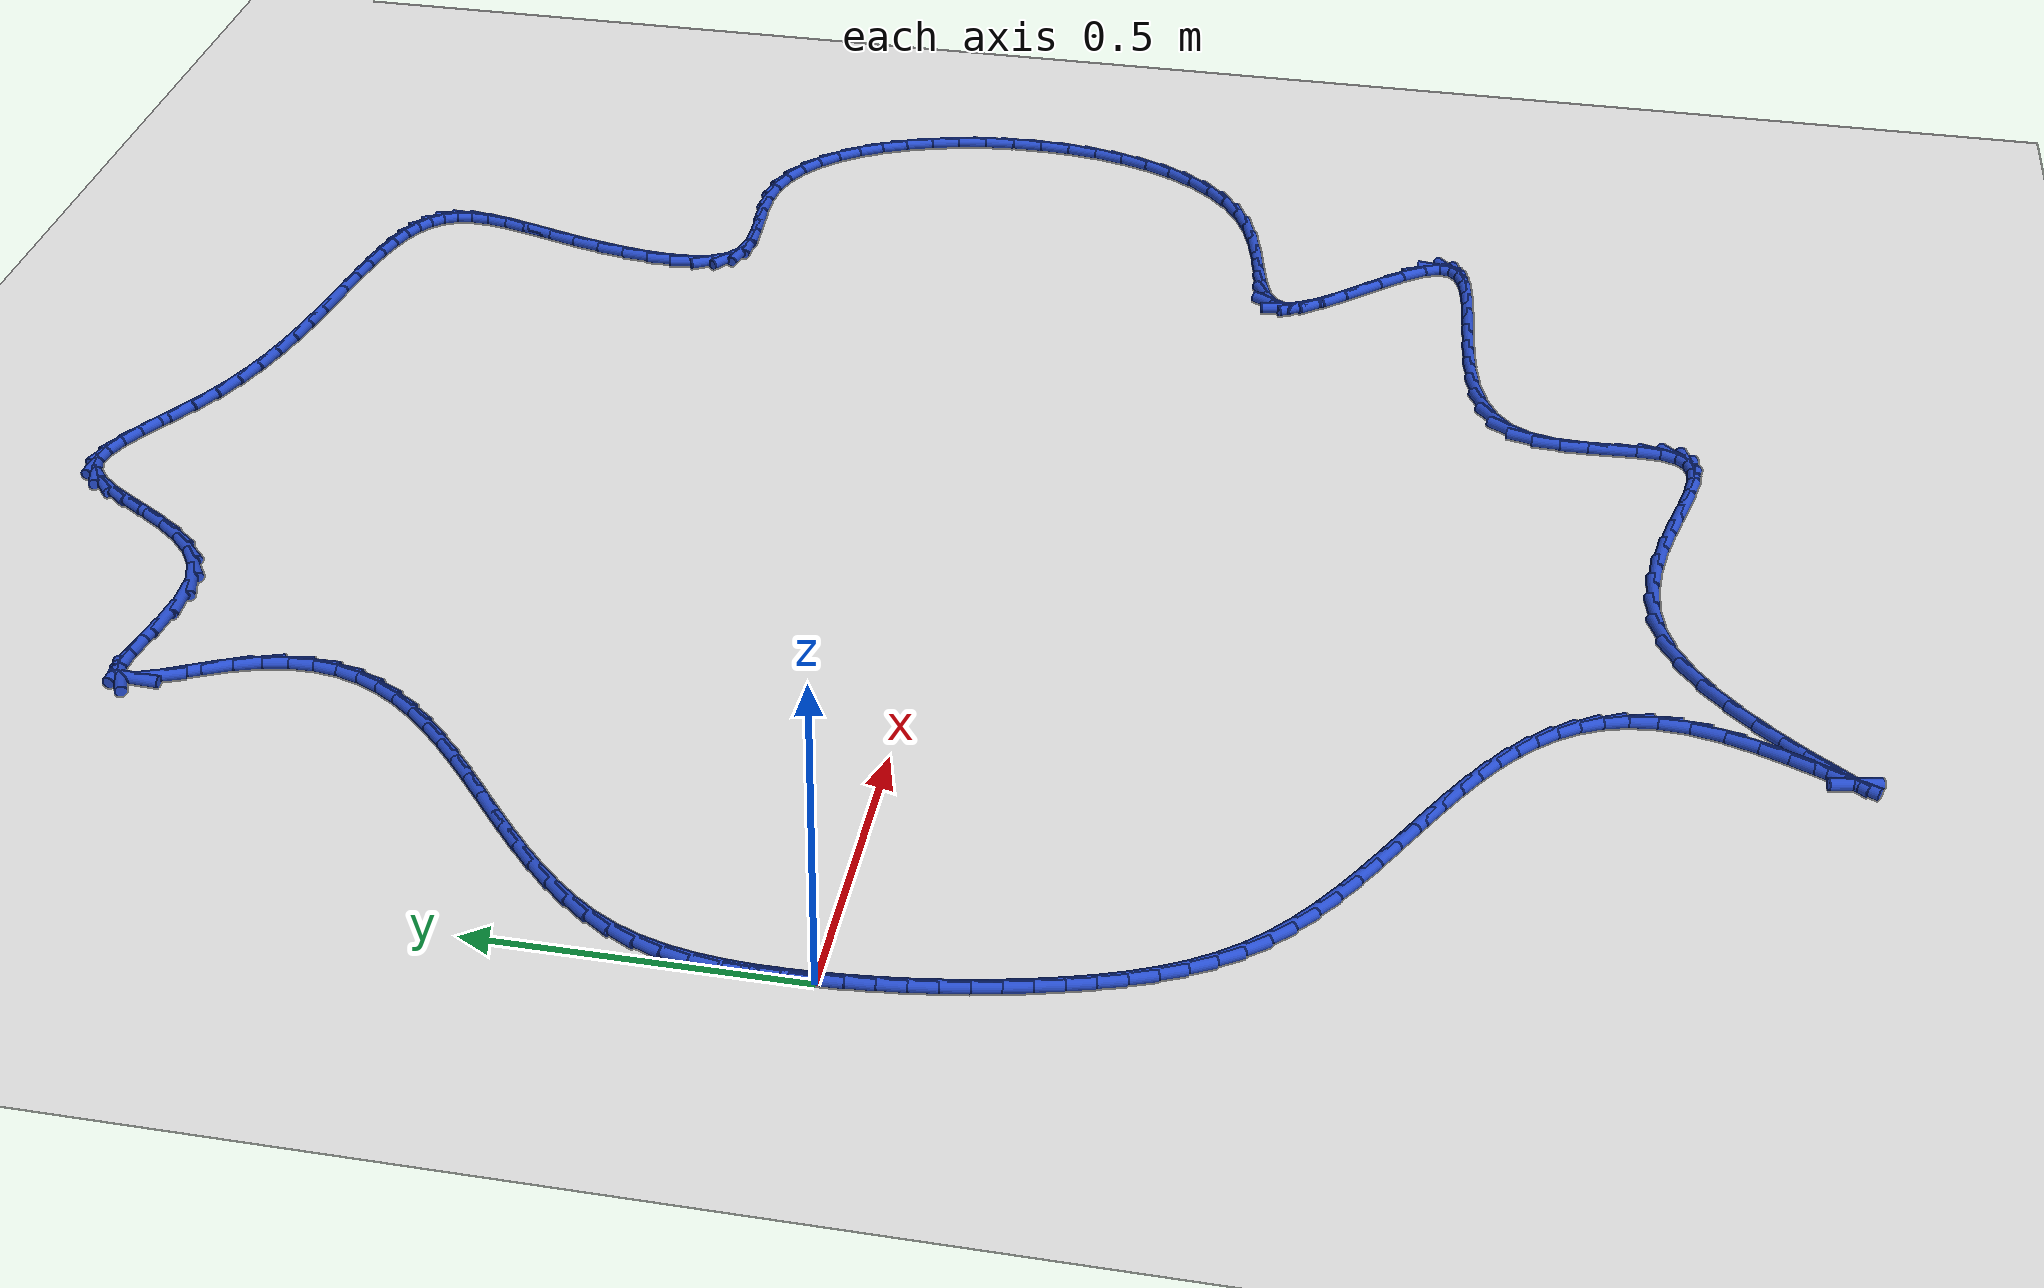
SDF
<sdf version="1.6">
 <world name="default">
  <light name="sun" type="directional">
   <pose>0 0 10 0 -0 0</pose>
   <diffuse>0.8 0.8 0.8 1</diffuse>
   <specular>0.2 0.2 0.2 1</specular>
   <attenuation>
    <range>1000</range>
    <constant>0.9</constant>
    <linear>0.01</linear>
    <quadratic>0.001</quadratic>
   </attenuation>
   <direction>-0.5 0.1 -0.9</direction>
  </light>
  <model name="ground_plane">
   <static>1</static>
   <link name="link">
    <collision name="collision">
     <geometry><plane><normal>0 0 1</normal><size>100 100</size></plane></geometry>
     <surface><friction><ode><mu>100</mu><mu2>50</mu2></ode></friction></surface>
    </collision>
    <visual name="visual">
     <cast_shadows>0</cast_shadows>
     <geometry><plane><normal>0 0 1</normal><size>100 100</size></plane></geometry>
     <material>
      <script><uri>file://media/materials/scripts/gazebo.material</uri><name>Gazebo/WhiteGlow</name></script>
     </material>
    </visual>
   </link>
  </model>
  <gravity>0 0 -9.8</gravity>
  <magnetic_field>6e-06 2.3e-05 -4.2e-05</magnetic_field>
  <atmosphere type="adiabatic"/>
  <physics name="default_physics" default="0" type="ode">
   <max_step_size>0.001</max_step_size>
   <real_time_factor>1</real_time_factor>
   <real_time_update_rate>1000</real_time_update_rate>
  </physics>
  <scene><ambient>0.4 0.4 0.4 1</ambient><background>0.7 0.7 0.7 1</background><shadows>1</shadows></scene>
  <spherical_coordinates>
   <surface_model>EARTH_WGS84</surface_model>
   <latitude_deg>0</latitude_deg>
   <longitude_deg>0</longitude_deg>
   <elevation>0</elevation>
   <heading_deg>0</heading_deg>
  </spherical_coordinates>
  <model name="line">
   <link name="link_0">
    <pose>-1.0842021724855044e-17 3.469446951953614e-17 0.01 0 1.57 -1.5368988126078118</pose>
    <collision name="collision">
     <geometry><cylinder><radius>0.01</radius><length>0.08</length></cylinder></geometry>
    </collision>
    <visual name="visual">
     <material>
      <script><name>Gazebo/Blue</name><uri>file://media/materials/scripts/gazebo.material</uri></script>
     </material>
     <geometry><cylinder><radius>0.01</radius><length>0.08</length></cylinder></geometry>
    </visual>
   </link>
   <link name="link_1">
    <pose>-0.0014516715959143498 0.04280890731460777 0.01 0 1.57 1.5659585013162598</pose>
    <collision name="collision">
     <geometry><cylinder><radius>0.01</radius><length>0.08</length></cylinder></geometry>
    </collision>
    <visual name="visual">
     <material>
      <script><name>Gazebo/Blue</name><uri>file://media/materials/scripts/gazebo.material</uri></script>
     </material>
     <geometry><cylinder><radius>0.01</radius><length>0.08</length></cylinder></geometry>
    </visual>
   </link>
   <link name="link_2">
    <pose>-0.0012441022626019952 0.08571407511581058 0.01 0 1.57 1.5150028420982957</pose>
    <collision name="collision">
     <geometry><cylinder><radius>0.01</radius><length>0.08</length></cylinder></geometry>
    </collision>
    <visual name="visual">
     <material>
      <script><name>Gazebo/Blue</name><uri>file://media/materials/scripts/gazebo.material</uri></script>
     </material>
     <geometry><cylinder><radius>0.01</radius><length>0.08</length></cylinder></geometry>
    </visual>
   </link>
   <link name="link_3">
    <pose>0.0011413706140954126 0.1284251034618987 0.01 0 1.57 1.451020490607723</pose>
    <collision name="collision">
     <geometry><cylinder><radius>0.01</radius><length>0.08</length></cylinder></geometry>
    </collision>
    <visual name="visual">
     <material>
      <script><name>Gazebo/Blue</name><uri>file://media/materials/scripts/gazebo.material</uri></script>
     </material>
     <geometry><cylinder><radius>0.01</radius><length>0.08</length></cylinder></geometry>
    </visual>
   </link>
   <link name="link_4">
    <pose>0.006223409648336242 0.1706515924111626 0.01 0 1.57 1.373239372330549</pose>
    <collision name="collision">
     <geometry><cylinder><radius>0.01</radius><length>0.08</length></cylinder></geometry>
    </collision>
    <visual name="visual">
     <material>
      <script><name>Gazebo/Blue</name><uri>file://media/materials/scripts/gazebo.material</uri></script>
     </material>
     <geometry><cylinder><radius>0.01</radius><length>0.08</length></cylinder></geometry>
    </visual>
   </link>
   <link name="link_5">
    <pose>0.014520677454278857 0.2121031420218925 0.01 0 1.57 1.2812648131036974</pose>
    <collision name="collision">
     <geometry><cylinder><radius>0.01</radius><length>0.08</length></cylinder></geometry>
    </collision>
    <visual name="visual">
     <material>
      <script><name>Gazebo/Blue</name><uri>file://media/materials/scripts/gazebo.material</uri></script>
     </material>
     <geometry><cylinder><radius>0.01</radius><length>0.08</length></cylinder></geometry>
    </visual>
   </link>
   <link name="link_6">
    <pose>0.026551836646081607 0.2524893523523788 0.01 0 1.57 1.175546476682977</pose>
    <collision name="collision">
     <geometry><cylinder><radius>0.01</radius><length>0.08</length></cylinder></geometry>
    </collision>
    <visual name="visual">
     <material>
      <script><name>Gazebo/Blue</name><uri>file://media/materials/scripts/gazebo.material</uri></script>
     </material>
     <geometry><cylinder><radius>0.01</radius><length>0.08</length></cylinder></geometry>
    </visual>
   </link>
   <link name="link_7">
    <pose>0.04283554983790288 0.29151982346091176 0.01 0 1.57 1.0616055408451468</pose>
    <collision name="collision">
     <geometry><cylinder><radius>0.01</radius><length>0.08</length></cylinder></geometry>
    </collision>
    <visual name="visual">
     <material>
      <script><name>Gazebo/Blue</name><uri>file://media/materials/scripts/gazebo.material</uri></script>
     </material>
     <geometry><cylinder><radius>0.01</radius><length>0.08</length></cylinder></geometry>
    </visual>
   </link>
   <link name="link_8">
    <pose>0.0637421741857241 0.32896697450251255 0.01 0 1.57 0.9607841583377517</pose>
    <collision name="collision">
     <geometry><cylinder><radius>0.01</radius><length>0.08</length></cylinder></geometry>
    </collision>
    <visual name="visual">
     <material>
      <script><name>Gazebo/Blue</name><uri>file://media/materials/scripts/gazebo.material</uri></script>
     </material>
     <geometry><cylinder><radius>0.01</radius><length>0.08</length></cylinder></geometry>
    </visual>
   </link>
   <link name="link_9">
    <pose>0.08887635882780928 0.36492756256705516 0.01 0 1.57 0.8790603935980738</pose>
    <collision name="collision">
     <geometry><cylinder><radius>0.01</radius><length>0.08</length></cylinder></geometry>
    </collision>
    <visual name="visual">
     <material>
      <script><name>Gazebo/Blue</name><uri>file://media/materials/scripts/gazebo.material</uri></script>
     </material>
     <geometry><cylinder><radius>0.01</radius><length>0.08</length></cylinder></geometry>
    </visual>
   </link>
   <link name="link_10">
    <pose>0.11759635489456768 0.39960271379785206 0.01 0 1.57 0.8149191896149264</pose>
    <collision name="collision">
     <geometry><cylinder><radius>0.01</radius><length>0.08</length></cylinder></geometry>
    </collision>
    <visual name="visual">
     <material>
      <script><name>Gazebo/Blue</name><uri>file://media/materials/scripts/gazebo.material</uri></script>
     </material>
     <geometry><cylinder><radius>0.01</radius><length>0.08</length></cylinder></geometry>
    </visual>
   </link>
   <link name="link_11">
    <pose>0.14926029587340603 0.43319360416933617 0.01 0 1.57 0.7665292209427014</pose>
    <collision name="collision">
     <geometry><cylinder><radius>0.01</radius><length>0.08</length></cylinder></geometry>
    </collision>
    <visual name="visual">
     <material>
      <script><name>Gazebo/Blue</name><uri>file://media/materials/scripts/gazebo.material</uri></script>
     </material>
     <geometry><cylinder><radius>0.01</radius><length>0.08</length></cylinder></geometry>
    </visual>
   </link>
   <link name="link_12">
    <pose>0.18322631525173097 0.46590140965594046 0.01 0 1.57 0.7322299686839594</pose>
    <collision name="collision">
     <geometry><cylinder><radius>0.01</radius><length>0.08</length></cylinder></geometry>
    </collision>
    <visual name="visual">
     <material>
      <script><name>Gazebo/Blue</name><uri>file://media/materials/scripts/gazebo.material</uri></script>
     </material>
     <geometry><cylinder><radius>0.01</radius><length>0.08</length></cylinder></geometry>
    </visual>
   </link>
   <link name="link_13">
    <pose>0.21885254651694955 0.4979273062320981 0.01 0 1.57 0.7107544021208096</pose>
    <collision name="collision">
     <geometry><cylinder><radius>0.01</radius><length>0.08</length></cylinder></geometry>
    </collision>
    <visual name="visual">
     <material>
      <script><name>Gazebo/Blue</name><uri>file://media/materials/scripts/gazebo.material</uri></script>
     </material>
     <geometry><cylinder><radius>0.01</radius><length>0.08</length></cylinder></geometry>
    </visual>
   </link>
   <link name="link_14">
    <pose>0.2554971231564685 0.529472469872242 0.01 0 1.57 0.7013132477878615</pose>
    <collision name="collision">
     <geometry><cylinder><radius>0.01</radius><length>0.08</length></cylinder></geometry>
    </collision>
    <visual name="visual">
     <material>
      <script><name>Gazebo/Blue</name><uri>file://media/materials/scripts/gazebo.material</uri></script>
     </material>
     <geometry><cylinder><radius>0.01</radius><length>0.08</length></cylinder></geometry>
    </visual>
   </link>
   <link name="link_15">
    <pose>0.2925181786576945 0.5607380765508049 0.01 0 1.57 0.7036232488913202</pose>
    <collision name="collision">
     <geometry><cylinder><radius>0.01</radius><length>0.08</length></cylinder></geometry>
    </collision>
    <visual name="visual">
     <material>
      <script><name>Gazebo/Blue</name><uri>file://media/materials/scripts/gazebo.material</uri></script>
     </material>
     <geometry><cylinder><radius>0.01</radius><length>0.08</length></cylinder></geometry>
    </visual>
   </link>
   <link name="link_16">
    <pose>0.32927384650803443 0.5919253022422201 0.01 0 1.57 0.7179233418604293</pose>
    <collision name="collision">
     <geometry><cylinder><radius>0.01</radius><length>0.08</length></cylinder></geometry>
    </collision>
    <visual name="visual">
     <material>
      <script><name>Gazebo/Blue</name><uri>file://media/materials/scripts/gazebo.material</uri></script>
     </material>
     <geometry><cylinder><radius>0.01</radius><length>0.08</length></cylinder></geometry>
    </visual>
   </link>
   <link name="link_17">
    <pose>0.365122260194895 0.6232353229209202 0.01 0 1.57 0.7449959446812255</pose>
    <collision name="collision">
     <geometry><cylinder><radius>0.01</radius><length>0.08</length></cylinder></geometry>
    </collision>
    <visual name="visual">
     <material>
      <script><name>Gazebo/Blue</name><uri>file://media/materials/scripts/gazebo.material</uri></script>
     </material>
     <geometry><cylinder><radius>0.01</radius><length>0.08</length></cylinder></geometry>
    </visual>
   </link>
   <link name="link_18">
    <pose>0.3994215532056832 0.6548693145613387 0.01 0 1.57 0.7861891197568008</pose>
    <collision name="collision">
     <geometry><cylinder><radius>0.01</radius><length>0.08</length></cylinder></geometry>
    </collision>
    <visual name="visual">
     <material>
      <script><name>Gazebo/Blue</name><uri>file://media/materials/scripts/gazebo.material</uri></script>
     </material>
     <geometry><cylinder><radius>0.01</radius><length>0.08</length></cylinder></geometry>
    </visual>
   </link>
   <link name="link_19">
    <pose>0.43152985902780555 0.6870284531379081 0.01 0 1.57 0.8434082346537224</pose>
    <collision name="collision">
     <geometry><cylinder><radius>0.01</radius><length>0.08</length></cylinder></geometry>
    </collision>
    <visual name="visual">
     <material>
      <script><name>Gazebo/Blue</name><uri>file://media/materials/scripts/gazebo.material</uri></script>
     </material>
     <geometry><cylinder><radius>0.01</radius><length>0.08</length></cylinder></geometry>
    </visual>
   </link>
   <link name="link_20">
    <pose>0.4608053111486691 0.7199139146250614 0.01 0 1.57 0.9190000260879077</pose>
    <collision name="collision">
     <geometry><cylinder><radius>0.01</radius><length>0.08</length></cylinder></geometry>
    </collision>
    <visual name="visual">
     <material>
      <script><name>Gazebo/Blue</name><uri>file://media/materials/scripts/gazebo.material</uri></script>
     </material>
     <geometry><cylinder><radius>0.01</radius><length>0.08</length></cylinder></geometry>
    </visual>
   </link>
   <link name="link_21">
    <pose>0.48660604305568045 0.7537268749972319 0.01 0 1.57 1.0153804073015564</pose>
    <collision name="collision">
     <geometry><cylinder><radius>0.01</radius><length>0.08</length></cylinder></geometry>
    </collision>
    <visual name="visual">
     <material>
      <script><name>Gazebo/Blue</name><uri>file://media/materials/scripts/gazebo.material</uri></script>
     </material>
     <geometry><cylinder><radius>0.01</radius><length>0.08</length></cylinder></geometry>
    </visual>
   </link>
   <link name="link_22">
    <pose>0.5082901882362464 0.7886685102288522 0.01 0 1.57 1.1341918419299764</pose>
    <collision name="collision">
     <geometry><cylinder><radius>0.01</radius><length>0.08</length></cylinder></geometry>
    </collision>
    <visual name="visual">
     <material>
      <script><name>Gazebo/Blue</name><uri>file://media/materials/scripts/gazebo.material</uri></script>
     </material>
     <geometry><cylinder><radius>0.01</radius><length>0.08</length></cylinder></geometry>
    </visual>
   </link>
   <link name="link_23">
    <pose>0.5252158801777738 0.8249399962943555 0.01 0 1.57 1.2748650645888</pose>
    <collision name="collision">
     <geometry><cylinder><radius>0.01</radius><length>0.08</length></cylinder></geometry>
    </collision>
    <visual name="visual">
     <material>
      <script><name>Gazebo/Blue</name><uri>file://media/materials/scripts/gazebo.material</uri></script>
     </material>
     <geometry><cylinder><radius>0.01</radius><length>0.08</length></cylinder></geometry>
    </visual>
   </link>
   <link name="link_24">
    <pose>0.5367412523676696 0.8627425091681747 0.01 0 1.57 1.4329825493292807</pose>
    <collision name="collision">
     <geometry><cylinder><radius>0.01</radius><length>0.08</length></cylinder></geometry>
    </collision>
    <visual name="visual">
     <material>
      <script><name>Gazebo/Blue</name><uri>file://media/materials/scripts/gazebo.material</uri></script>
     </material>
     <geometry><cylinder><radius>0.01</radius><length>0.08</length></cylinder></geometry>
    </visual>
   </link>
   <link name="link_25">
    <pose>0.5422244382933404 0.9022772248247433 0.01 0 1.57 -1.541845603366805</pose>
    <collision name="collision">
     <geometry><cylinder><radius>0.01</radius><length>0.08</length></cylinder></geometry>
    </collision>
    <visual name="visual">
     <material>
      <script><name>Gazebo/Blue</name><uri>file://media/materials/scripts/gazebo.material</uri></script>
     </material>
     <geometry><cylinder><radius>0.01</radius><length>0.08</length></cylinder></geometry>
    </visual>
   </link>
   <link name="link_26">
    <pose>0.541023571442193 0.9437453192384933 0.01 0 1.57 -1.377676887726726</pose>
    <collision name="collision">
     <geometry><cylinder><radius>0.01</radius><length>0.08</length></cylinder></geometry>
    </collision>
    <visual name="visual">
     <material>
      <script><name>Gazebo/Blue</name><uri>file://media/materials/scripts/gazebo.material</uri></script>
     </material>
     <geometry><cylinder><radius>0.01</radius><length>0.08</length></cylinder></geometry>
    </visual>
   </link>
   <link name="link_27">
    <pose>0.5324967853016342 0.9873479683838582 0.01 0 1.57 -1.2265032268384348</pose>
    <collision name="collision">
     <geometry><cylinder><radius>0.01</radius><length>0.08</length></cylinder></geometry>
    </collision>
    <visual name="visual">
     <material>
      <script><name>Gazebo/Blue</name><uri>file://media/materials/scripts/gazebo.material</uri></script>
     </material>
     <geometry><cylinder><radius>0.01</radius><length>0.08</length></cylinder></geometry>
    </visual>
   </link>
   <link name="link_28">
    <pose>0.5160306476102455 1.0332690683000556 0.01 0 1.57 -1.1244846671152116</pose>
    <collision name="collision">
     <geometry><cylinder><radius>0.01</radius><length>0.08</length></cylinder></geometry>
    </collision>
    <visual name="visual">
     <material>
      <script><name>Gazebo/Blue</name><uri>file://media/materials/scripts/gazebo.material</uri></script>
     </material>
     <geometry><cylinder><radius>0.01</radius><length>0.08</length></cylinder></geometry>
    </visual>
   </link>
   <link name="link_29">
    <pose>0.49361694083242313 1.0801092856523826 0.01 0 1.57 -1.1081911090037806</pose>
    <collision name="collision">
     <geometry><cylinder><radius>0.01</radius><length>0.08</length></cylinder></geometry>
    </collision>
    <visual name="visual">
     <material>
      <script><name>Gazebo/Blue</name><uri>file://media/materials/scripts/gazebo.material</uri></script>
     </material>
     <geometry><cylinder><radius>0.01</radius><length>0.08</length></cylinder></geometry>
    </visual>
   </link>
   <link name="link_30">
    <pose>0.47191054218108175 1.1236354521419556 0.01 0 1.57 -1.2003290559949678</pose>
    <collision name="collision">
     <geometry><cylinder><radius>0.01</radius><length>0.08</length></cylinder></geometry>
    </collision>
    <visual name="visual">
     <material>
      <script><name>Gazebo/Blue</name><uri>file://media/materials/scripts/gazebo.material</uri></script>
     </material>
     <geometry><cylinder><radius>0.01</radius><length>0.08</length></cylinder></geometry>
    </visual>
   </link>
   <link name="link_31">
    <pose>0.4580505939184414 1.1593201040925327 0.01 0 1.57 1.5233392924097766</pose>
    <collision name="collision">
     <geometry><cylinder><radius>0.01</radius><length>0.08</length></cylinder></geometry>
    </collision>
    <visual name="visual">
     <material>
      <script><name>Gazebo/Blue</name><uri>file://media/materials/scripts/gazebo.material</uri></script>
     </material>
     <geometry><cylinder><radius>0.01</radius><length>0.08</length></cylinder></geometry>
    </visual>
   </link>
   <link name="link_32">
    <pose>0.45915857684002037 1.1826496488551725 0.01 0 1.57 0.4292926324782675</pose>
    <collision name="collision">
     <geometry><cylinder><radius>0.01</radius><length>0.08</length></cylinder></geometry>
    </collision>
    <visual name="visual">
     <material>
      <script><name>Gazebo/Blue</name><uri>file://media/materials/scripts/gazebo.material</uri></script>
     </material>
     <geometry><cylinder><radius>0.01</radius><length>0.08</length></cylinder></geometry>
    </visual>
   </link>
   <link name="link_33">
    <pose>0.47901114767781816 1.1917374639339968 0.01 0 1.57 -0.037774600823491385</pose>
    <collision name="collision">
     <geometry><cylinder><radius>0.01</radius><length>0.08</length></cylinder></geometry>
    </collision>
    <visual name="visual">
     <material>
      <script><name>Gazebo/Blue</name><uri>file://media/materials/scripts/gazebo.material</uri></script>
     </material>
     <geometry><cylinder><radius>0.01</radius><length>0.08</length></cylinder></geometry>
    </visual>
   </link>
   <link name="link_34">
    <pose>0.5141094330994319 1.190411009237462 0.01 0 1.57 -0.15483144776434213</pose>
    <collision name="collision">
     <geometry><cylinder><radius>0.01</radius><length>0.08</length></cylinder></geometry>
    </collision>
    <visual name="visual">
     <material>
      <script><name>Gazebo/Blue</name><uri>file://media/materials/scripts/gazebo.material</uri></script>
     </material>
     <geometry><cylinder><radius>0.01</radius><length>0.08</length></cylinder></geometry>
    </visual>
   </link>
   <link name="link_35">
    <pose>0.559998509025957 1.1832486113050262 0.01 0 1.57 -0.15985035755464888</pose>
    <collision name="collision">
     <geometry><cylinder><radius>0.01</radius><length>0.08</length></cylinder></geometry>
    </collision>
    <visual name="visual">
     <material>
      <script><name>Gazebo/Blue</name><uri>file://media/materials/scripts/gazebo.material</uri></script>
     </material>
     <geometry><cylinder><radius>0.01</radius><length>0.08</length></cylinder></geometry>
    </visual>
   </link>
   <link name="link_36">
    <pose>0.6122234513784878 1.1748285966761507 0.01 0 1.57 -0.0939691987243753</pose>
    <collision name="collision">
     <geometry><cylinder><radius>0.01</radius><length>0.08</length></cylinder></geometry>
    </collision>
    <visual name="visual">
     <material>
      <script><name>Gazebo/Blue</name><uri>file://media/materials/scripts/gazebo.material</uri></script>
     </material>
     <geometry><cylinder><radius>0.01</radius><length>0.08</length></cylinder></geometry>
    </visual>
   </link>
   <link name="link_37">
    <pose>0.6663293360781197 1.1697292918902946 0.01 0 1.57 0.054276702313486844</pose>
    <collision name="collision">
     <geometry><cylinder><radius>0.01</radius><length>0.08</length></cylinder></geometry>
    </collision>
    <visual name="visual">
     <material>
      <script><name>Gazebo/Blue</name><uri>file://media/materials/scripts/gazebo.material</uri></script>
     </material>
     <geometry><cylinder><radius>0.01</radius><length>0.08</length></cylinder></geometry>
    </visual>
   </link>
   <link name="link_38">
    <pose>0.7178612390459476 1.1725290234869181 0.01 0 1.57 0.30872842150869706</pose>
    <collision name="collision">
     <geometry><cylinder><radius>0.01</radius><length>0.08</length></cylinder></geometry>
    </collision>
    <visual name="visual">
     <material>
      <script><name>Gazebo/Blue</name><uri>file://media/materials/scripts/gazebo.material</uri></script>
     </material>
     <geometry><cylinder><radius>0.01</radius><length>0.08</length></cylinder></geometry>
    </visual>
   </link>
   <link name="link_39">
    <pose>0.7630298515190208 1.186934469309282 0.01 0 1.57 0.5718923769587057</pose>
    <collision name="collision">
     <geometry><cylinder><radius>0.01</radius><length>0.08</length></cylinder></geometry>
    </collision>
    <visual name="visual">
     <material>
      <script><name>Gazebo/Blue</name><uri>file://media/materials/scripts/gazebo.material</uri></script>
     </material>
     <geometry><cylinder><radius>0.01</radius><length>0.08</length></cylinder></geometry>
    </visual>
   </link>
   <link name="link_40">
    <pose>0.8017219592300585 1.2118383209574786 0.01 0 1.57 0.7744549400300602</pose>
    <collision name="collision">
     <geometry><cylinder><radius>0.01</radius><length>0.08</length></cylinder></geometry>
    </collision>
    <visual name="visual">
     <material>
      <script><name>Gazebo/Blue</name><uri>file://media/materials/scripts/gazebo.material</uri></script>
     </material>
     <geometry><cylinder><radius>0.01</radius><length>0.08</length></cylinder></geometry>
    </visual>
   </link>
   <link name="link_41">
    <pose>0.8350864681323628 1.2444804753642456 0.01 0 1.57 0.9109494527060492</pose>
    <collision name="collision">
     <geometry><cylinder><radius>0.01</radius><length>0.08</length></cylinder></geometry>
    </collision>
    <visual name="visual">
     <material>
      <script><name>Gazebo/Blue</name><uri>file://media/materials/scripts/gazebo.material</uri></script>
     </material>
     <geometry><cylinder><radius>0.01</radius><length>0.08</length></cylinder></geometry>
    </visual>
   </link>
   <link name="link_42">
    <pose>0.8642734231441511 1.282099337944235 0.01 0 1.57 0.9897171869193896</pose>
    <collision name="collision">
     <geometry><cylinder><radius>0.01</radius><length>0.08</length></cylinder></geometry>
    </collision>
    <visual name="visual">
     <material>
      <script><name>Gazebo/Blue</name><uri>file://media/materials/scripts/gazebo.material</uri></script>
     </material>
     <geometry><cylinder><radius>0.01</radius><length>0.08</length></cylinder></geometry>
    </visual>
   </link>
   <link name="link_43">
    <pose>0.8904328691836405 1.3219333141121001 0.01 0 1.57 1.0172040169870904</pose>
    <collision name="collision">
     <geometry><cylinder><radius>0.01</radius><length>0.08</length></cylinder></geometry>
    </collision>
    <visual name="visual">
     <material>
      <script><name>Gazebo/Blue</name><uri>file://media/materials/scripts/gazebo.material</uri></script>
     </material>
     <geometry><cylinder><radius>0.01</radius><length>0.08</length></cylinder></geometry>
    </visual>
   </link>
   <link name="link_44">
    <pose>0.9147148511690473 1.3612208092824931 0.01 0 1.57 0.9911467858185824</pose>
    <collision name="collision">
     <geometry><cylinder><radius>0.01</radius><length>0.08</length></cylinder></geometry>
    </collision>
    <visual name="visual">
     <material>
      <script><name>Gazebo/Blue</name><uri>file://media/materials/scripts/gazebo.material</uri></script>
     </material>
     <geometry><cylinder><radius>0.01</radius><length>0.08</length></cylinder></geometry>
    </visual>
   </link>
   <link name="link_45">
    <pose>0.9382694140185884 1.3972002288700662 0.01 0 1.57 0.8950493228421793</pose>
    <collision name="collision">
     <geometry><cylinder><radius>0.01</radius><length>0.08</length></cylinder></geometry>
    </collision>
    <visual name="visual">
     <material>
      <script><name>Gazebo/Blue</name><uri>file://media/materials/scripts/gazebo.material</uri></script>
     </material>
     <geometry><cylinder><radius>0.01</radius><length>0.08</length></cylinder></geometry>
    </visual>
   </link>
   <link name="link_46">
    <pose>0.9622466026504807 1.4271099782894723 0.01 0 1.57 0.689796568144273</pose>
    <collision name="collision">
     <geometry><cylinder><radius>0.01</radius><length>0.08</length></cylinder></geometry>
    </collision>
    <visual name="visual">
     <material>
      <script><name>Gazebo/Blue</name><uri>file://media/materials/scripts/gazebo.material</uri></script>
     </material>
     <geometry><cylinder><radius>0.01</radius><length>0.08</length></cylinder></geometry>
    </visual>
   </link>
   <link name="link_47">
    <pose>0.987796461982941 1.4481884629553647 0.01 0 1.57 0.3268157725394755</pose>
    <collision name="collision">
     <geometry><cylinder><radius>0.01</radius><length>0.08</length></cylinder></geometry>
    </collision>
    <visual name="visual">
     <material>
      <script><name>Gazebo/Blue</name><uri>file://media/materials/scripts/gazebo.material</uri></script>
     </material>
     <geometry><cylinder><radius>0.01</radius><length>0.08</length></cylinder></geometry>
    </visual>
   </link>
   <link name="link_48">
    <pose>1.0160465663643046 1.4577644268344314 0.01 0 1.57 -0.06968947523810112</pose>
    <collision name="collision">
     <geometry><cylinder><radius>0.01</radius><length>0.08</length></cylinder></geometry>
    </collision>
    <visual name="visual">
     <material>
      <script><name>Gazebo/Blue</name><uri>file://media/materials/scripts/gazebo.material</uri></script>
     </material>
     <geometry><cylinder><radius>0.01</radius><length>0.08</length></cylinder></geometry>
    </visual>
   </link>
   <link name="link_49">
    <pose>1.0475274286184637 1.4555669835270322 0.01 0 1.57 -0.3247370791920183</pose>
    <collision name="collision">
     <geometry><cylinder><radius>0.01</radius><length>0.08</length></cylinder></geometry>
    </collision>
    <visual name="visual">
     <material>
      <script><name>Gazebo/Blue</name><uri>file://media/materials/scripts/gazebo.material</uri></script>
     </material>
     <geometry><cylinder><radius>0.01</radius><length>0.08</length></cylinder></geometry>
    </visual>
   </link>
   <link name="link_50">
    <pose>1.082124197316028 1.443919807985771 0.01 0 1.57 -0.46068617987208016</pose>
    <collision name="collision">
     <geometry><cylinder><radius>0.01</radius><length>0.08</length></cylinder></geometry>
    </collision>
    <visual name="visual">
     <material>
      <script><name>Gazebo/Blue</name><uri>file://media/materials/scripts/gazebo.material</uri></script>
     </material>
     <geometry><cylinder><radius>0.01</radius><length>0.08</length></cylinder></geometry>
    </visual>
   </link>
   <link name="link_51">
    <pose>1.1196898715803825 1.4252758257575457 0.01 0 1.57 -0.5211828625674896</pose>
    <collision name="collision">
     <geometry><cylinder><radius>0.01</radius><length>0.08</length></cylinder></geometry>
    </collision>
    <visual name="visual">
     <material>
      <script><name>Gazebo/Blue</name><uri>file://media/materials/scripts/gazebo.material</uri></script>
     </material>
     <geometry><cylinder><radius>0.01</radius><length>0.08</length></cylinder></geometry>
    </visual>
   </link>
   <link name="link_52">
    <pose>1.160077450534908 1.4020879623892533 0.01 0 1.57 -0.530825549980629</pose>
    <collision name="collision">
     <geometry><cylinder><radius>0.01</radius><length>0.08</length></cylinder></geometry>
    </collision>
    <visual name="visual">
     <material>
      <script><name>Gazebo/Blue</name><uri>file://media/materials/scripts/gazebo.material</uri></script>
     </material>
     <geometry><cylinder><radius>0.01</radius><length>0.08</length></cylinder></geometry>
    </visual>
   </link>
   <link name="link_53">
    <pose>1.20313993330299 1.3768091434277914 0.01 0 1.57 -0.500180867023884</pose>
    <collision name="collision">
     <geometry><cylinder><radius>0.01</radius><length>0.08</length></cylinder></geometry>
    </collision>
    <visual name="visual">
     <material>
      <script><name>Gazebo/Blue</name><uri>file://media/materials/scripts/gazebo.material</uri></script>
     </material>
     <geometry><cylinder><radius>0.01</radius><length>0.08</length></cylinder></geometry>
    </visual>
   </link>
   <link name="link_54">
    <pose>1.2487303190080101 1.3518922944200582 0.01 0 1.57 -0.43292029826082484</pose>
    <collision name="collision">
     <geometry><cylinder><radius>0.01</radius><length>0.08</length></cylinder></geometry>
    </collision>
    <visual name="visual">
     <material>
      <script><name>Gazebo/Blue</name><uri>file://media/materials/scripts/gazebo.material</uri></script>
     </material>
     <geometry><cylinder><radius>0.01</radius><length>0.08</length></cylinder></geometry>
    </visual>
   </link>
   <link name="link_55">
    <pose>1.2966925006008096 1.3297260778118267 0.01 0 1.57 -0.3538817943182508</pose>
    <collision name="collision">
     <geometry><cylinder><radius>0.01</radius><length>0.08</length></cylinder></geometry>
    </collision>
    <visual name="visual">
     <material>
      <script><name>Gazebo/Blue</name><uri>file://media/materials/scripts/gazebo.material</uri></script>
     </material>
     <geometry><cylinder><radius>0.01</radius><length>0.08</length></cylinder></geometry>
    </visual>
   </link>
   <link name="link_56">
    <pose>1.3466669813376237 1.3112638161789045 0.01 0 1.57 -0.2876853802730694</pose>
    <collision name="collision">
     <geometry><cylinder><radius>0.01</radius><length>0.08</length></cylinder></geometry>
    </collision>
    <visual name="visual">
     <material>
      <script><name>Gazebo/Blue</name><uri>file://media/materials/scripts/gazebo.material</uri></script>
     </material>
     <geometry><cylinder><radius>0.01</radius><length>0.08</length></cylinder></geometry>
    </visual>
   </link>
   <link name="link_57">
    <pose>1.3980941813938965 1.2960468273064274 0.01 0 1.57 -0.234372294279772</pose>
    <collision name="collision">
     <geometry><cylinder><radius>0.01</radius><length>0.08</length></cylinder></geometry>
    </collision>
    <visual name="visual">
     <material>
      <script><name>Gazebo/Blue</name><uri>file://media/materials/scripts/gazebo.material</uri></script>
     </material>
     <geometry><cylinder><radius>0.01</radius><length>0.08</length></cylinder></geometry>
    </visual>
   </link>
   <link name="link_58">
    <pose>1.450406076150996 1.2835568332873375 0.01 0 1.57 -0.1929256856500964</pose>
    <collision name="collision">
     <geometry><cylinder><radius>0.01</radius><length>0.08</length></cylinder></geometry>
    </collision>
    <visual name="visual">
     <material>
      <script><name>Gazebo/Blue</name><uri>file://media/materials/scripts/gazebo.material</uri></script>
     </material>
     <geometry><cylinder><radius>0.01</radius><length>0.08</length></cylinder></geometry>
    </visual>
   </link>
   <link name="link_59">
    <pose>1.5030346409902902 1.273275556214578 0.01 0 1.57 -0.16257110364568542</pose>
    <collision name="collision">
     <geometry><cylinder><radius>0.01</radius><length>0.08</length></cylinder></geometry>
    </collision>
    <visual name="visual">
     <material>
      <script><name>Gazebo/Blue</name><uri>file://media/materials/scripts/gazebo.material</uri></script>
     </material>
     <geometry><cylinder><radius>0.01</radius><length>0.08</length></cylinder></geometry>
    </visual>
   </link>
   <link name="link_60">
    <pose>1.5554118512931465 1.264684718181093 0.01 0 1.57 -0.14290949893314753</pose>
    <collision name="collision">
     <geometry><cylinder><radius>0.01</radius><length>0.08</length></cylinder></geometry>
    </collision>
    <visual name="visual">
     <material>
      <script><name>Gazebo/Blue</name><uri>file://media/materials/scripts/gazebo.material</uri></script>
     </material>
     <geometry><cylinder><radius>0.01</radius><length>0.08</length></cylinder></geometry>
    </visual>
   </link>
   <link name="link_61">
    <pose>1.6069696824409316 1.2572660412798244 0.01 0 1.57 -0.13402793256331727</pose>
    <collision name="collision">
     <geometry><cylinder><radius>0.01</radius><length>0.08</length></cylinder></geometry>
    </collision>
    <visual name="visual">
     <material>
      <script><name>Gazebo/Blue</name><uri>file://media/materials/scripts/gazebo.material</uri></script>
     </material>
     <geometry><cylinder><radius>0.01</radius><length>0.08</length></cylinder></geometry>
    </visual>
   </link>
   <link name="link_62">
    <pose>1.6571401098150127 1.2505012476037156 0.01 0 1.57 -0.13663554945352568</pose>
    <collision name="collision">
     <geometry><cylinder><radius>0.01</radius><length>0.08</length></cylinder></geometry>
    </collision>
    <visual name="visual">
     <material>
      <script><name>Gazebo/Blue</name><uri>file://media/materials/scripts/gazebo.material</uri></script>
     </material>
     <geometry><cylinder><radius>0.01</radius><length>0.08</length></cylinder></geometry>
    </visual>
   </link>
   <link name="link_63">
    <pose>1.705355108796759 1.2438720592457095 0.01 0 1.57 -0.15227285731366189</pose>
    <collision name="collision">
     <geometry><cylinder><radius>0.01</radius><length>0.08</length></cylinder></geometry>
    </collision>
    <visual name="visual">
     <material>
      <script><name>Gazebo/Blue</name><uri>file://media/materials/scripts/gazebo.material</uri></script>
     </material>
     <geometry><cylinder><radius>0.01</radius><length>0.08</length></cylinder></geometry>
    </visual>
   </link>
   <link name="link_64">
    <pose>1.7510466547675358 1.2368601982987497 0.01 0 1.57 -0.18365341744095673</pose>
    <collision name="collision">
     <geometry><cylinder><radius>0.01</radius><length>0.08</length></cylinder></geometry>
    </collision>
    <visual name="visual">
     <material>
      <script><name>Gazebo/Blue</name><uri>file://media/materials/scripts/gazebo.material</uri></script>
     </material>
     <geometry><cylinder><radius>0.01</radius><length>0.08</length></cylinder></geometry>
    </visual>
   </link>
   <link name="link_65">
    <pose>1.793646723108711 1.2289473868557783 0.01 0 1.57 -0.2352123937676256</pose>
    <collision name="collision">
     <geometry><cylinder><radius>0.01</radius><length>0.08</length></cylinder></geometry>
    </collision>
    <visual name="visual">
     <material>
      <script><name>Gazebo/Blue</name><uri>file://media/materials/scripts/gazebo.material</uri></script>
     </material>
     <geometry><cylinder><radius>0.01</radius><length>0.08</length></cylinder></geometry>
    </visual>
   </link>
   <link name="link_66">
    <pose>1.8325872892016535 1.2196153470097393 0.01 0 1.57 -0.31391420819106536</pose>
    <collision name="collision">
     <geometry><cylinder><radius>0.01</radius><length>0.08</length></cylinder></geometry>
    </collision>
    <visual name="visual">
     <material>
      <script><name>Gazebo/Blue</name><uri>file://media/materials/scripts/gazebo.material</uri></script>
     </material>
     <geometry><cylinder><radius>0.01</radius><length>0.08</length></cylinder></geometry>
    </visual>
   </link>
   <link name="link_67">
    <pose>1.8673003284277283 1.2083458008535752 0.01 0 1.57 -0.43012541419790107</pose>
    <collision name="collision">
     <geometry><cylinder><radius>0.01</radius><length>0.08</length></cylinder></geometry>
    </collision>
    <visual name="visual">
     <material>
      <script><name>Gazebo/Blue</name><uri>file://media/materials/scripts/gazebo.material</uri></script>
     </material>
     <geometry><cylinder><radius>0.01</radius><length>0.08</length></cylinder></geometry>
    </visual>
   </link>
   <link name="link_68">
    <pose>1.897217816168304 1.194620470480229 0.01 0 1.57 -0.5972527545270093</pose>
    <collision name="collision">
     <geometry><cylinder><radius>0.01</radius><length>0.08</length></cylinder></geometry>
    </collision>
    <visual name="visual">
     <material>
      <script><name>Gazebo/Blue</name><uri>file://media/materials/scripts/gazebo.material</uri></script>
     </material>
     <geometry><cylinder><radius>0.01</radius><length>0.08</length></cylinder></geometry>
    </visual>
   </link>
   <link name="link_69">
    <pose>1.9217717278047488 1.1779210779826441 0.01 0 1.57 -0.8258105247849534</pose>
    <collision name="collision">
     <geometry><cylinder><radius>0.01</radius><length>0.08</length></cylinder></geometry>
    </collision>
    <visual name="visual">
     <material>
      <script><name>Gazebo/Blue</name><uri>file://media/materials/scripts/gazebo.material</uri></script>
     </material>
     <geometry><cylinder><radius>0.01</radius><length>0.08</length></cylinder></geometry>
    </visual>
   </link>
   <link name="link_70">
    <pose>1.9403940387184286 1.1577293454537632 0.01 0 1.57 -1.1064379540791758</pose>
    <collision name="collision">
     <geometry><cylinder><radius>0.01</radius><length>0.08</length></cylinder></geometry>
    </collision>
    <visual name="visual">
     <material>
      <script><name>Gazebo/Blue</name><uri>file://media/materials/scripts/gazebo.material</uri></script>
     </material>
     <geometry><cylinder><radius>0.01</radius><length>0.08</length></cylinder></geometry>
    </visual>
   </link>
   <link name="link_71">
    <pose>1.9525167242907115 1.1335269949865294 0.01 0 1.57 -1.3958731332271956</pose>
    <collision name="collision">
     <geometry><cylinder><radius>0.01</radius><length>0.08</length></cylinder></geometry>
    </collision>
    <visual name="visual">
     <material>
      <script><name>Gazebo/Blue</name><uri>file://media/materials/scripts/gazebo.material</uri></script>
     </material>
     <geometry><cylinder><radius>0.01</radius><length>0.08</length></cylinder></geometry>
    </visual>
   </link>
   <link name="link_72">
    <pose>1.9575926544718563 1.1048055152909322 0.01 0 1.57 1.5206338667820836</pose>
    <collision name="collision">
     <geometry><cylinder><radius>0.01</radius><length>0.08</length></cylinder></geometry>
    </collision>
    <visual name="visual">
     <material>
      <script><name>Gazebo/Blue</name><uri>file://media/materials/scripts/gazebo.material</uri></script>
     </material>
     <geometry><cylinder><radius>0.01</radius><length>0.08</length></cylinder></geometry>
    </visual>
   </link>
   <link name="link_73">
    <pose>1.9559180857748728 1.0714506139585798 0.01 0 1.57 1.386264278225284</pose>
    <collision name="collision">
     <geometry><cylinder><radius>0.01</radius><length>0.08</length></cylinder></geometry>
    </collision>
    <visual name="visual">
     <material>
      <script><name>Gazebo/Blue</name><uri>file://media/materials/scripts/gazebo.material</uri></script>
     </material>
     <geometry><cylinder><radius>0.01</radius><length>0.08</length></cylinder></geometry>
    </visual>
   </link>
   <link name="link_74">
    <pose>1.9489032090766314 1.0338686779213908 0.01 0 1.57 1.3138650329889607</pose>
    <collision name="collision">
     <geometry><cylinder><radius>0.01</radius><length>0.08</length></cylinder></geometry>
    </collision>
    <visual name="visual">
     <material>
      <script><name>Gazebo/Blue</name><uri>file://media/materials/scripts/gazebo.material</uri></script>
     </material>
     <geometry><cylinder><radius>0.01</radius><length>0.08</length></cylinder></geometry>
    </visual>
   </link>
   <link name="link_75">
    <pose>1.9380345358386093 0.9925017681625857 0.01 0 1.57 1.2829752232633198</pose>
    <collision name="collision">
     <geometry><cylinder><radius>0.01</radius><length>0.08</length></cylinder></geometry>
    </collision>
    <visual name="visual">
     <material>
      <script><name>Gazebo/Blue</name><uri>file://media/materials/scripts/gazebo.material</uri></script>
     </material>
     <geometry><cylinder><radius>0.01</radius><length>0.08</length></cylinder></geometry>
    </visual>
   </link>
   <link name="link_76">
    <pose>1.924798577522284 0.9477919456653863 0.01 0 1.57 1.2825504020763367</pose>
    <collision name="collision">
     <geometry><cylinder><radius>0.01</radius><length>0.08</length></cylinder></geometry>
    </collision>
    <visual name="visual">
     <material>
      <script><name>Gazebo/Blue</name><uri>file://media/materials/scripts/gazebo.material</uri></script>
     </material>
     <geometry><cylinder><radius>0.01</radius><length>0.08</length></cylinder></geometry>
    </visual>
   </link>
   <link name="link_77">
    <pose>1.9106818455891352 0.9001812714130155 0.01 0 1.57 1.3070906704318568</pose>
    <collision name="collision">
     <geometry><cylinder><radius>0.01</radius><length>0.08</length></cylinder></geometry>
    </collision>
    <visual name="visual">
     <material>
      <script><name>Gazebo/Blue</name><uri>file://media/materials/scripts/gazebo.material</uri></script>
     </material>
     <geometry><cylinder><radius>0.01</radius><length>0.08</length></cylinder></geometry>
    </visual>
   </link>
   <link name="link_78">
    <pose>1.8971677981541775 0.8501280150739561 0.01 0 1.57 1.349726772207351</pose>
    <collision name="collision">
     <geometry><cylinder><radius>0.01</radius><length>0.08</length></cylinder></geometry>
    </collision>
    <visual name="visual">
     <material>
      <script><name>Gazebo/Blue</name><uri>file://media/materials/scripts/gazebo.material</uri></script>
     </material>
     <geometry><cylinder><radius>0.01</radius><length>0.08</length></cylinder></geometry>
    </visual>
   </link>
   <link name="link_79">
    <pose>1.8856180717497217 0.7987371360118116 0.01 0 1.57 1.4071512008913252</pose>
    <collision name="collision">
     <geometry><cylinder><radius>0.01</radius><length>0.08</length></cylinder></geometry>
    </collision>
    <visual name="visual">
     <material>
      <script><name>Gazebo/Blue</name><uri>file://media/materials/scripts/gazebo.material</uri></script>
     </material>
     <geometry><cylinder><radius>0.01</radius><length>0.08</length></cylinder></geometry>
    </visual>
   </link>
   <link name="link_80">
    <pose>1.8772342217308982 0.7479633842870775 0.01 0 1.57 1.4873395987821931</pose>
    <collision name="collision">
     <geometry><cylinder><radius>0.01</radius><length>0.08</length></cylinder></geometry>
    </collision>
    <visual name="visual">
     <material>
      <script><name>Gazebo/Blue</name><uri>file://media/materials/scripts/gazebo.material</uri></script>
     </material>
     <geometry><cylinder><radius>0.01</radius><length>0.08</length></cylinder></geometry>
    </visual>
   </link>
   <link name="link_81">
    <pose>1.8732069188060938 0.6998192910916903 0.01 0 1.57 -1.535871490479705</pose>
    <collision name="collision">
     <geometry><cylinder><radius>0.01</radius><length>0.08</length></cylinder></geometry>
    </collision>
    <visual name="visual">
     <material>
      <script><name>Gazebo/Blue</name><uri>file://media/materials/scripts/gazebo.material</uri></script>
     </material>
     <geometry><cylinder><radius>0.01</radius><length>0.08</length></cylinder></geometry>
    </visual>
   </link>
   <link name="link_82">
    <pose>1.8747268336836975 0.6563173876175861 0.01 0 1.57 -1.3503296436587149</pose>
    <collision name="collision">
     <geometry><cylinder><radius>0.01</radius><length>0.08</length></cylinder></geometry>
    </collision>
    <visual name="visual">
     <material>
      <script><name>Gazebo/Blue</name><uri>file://media/materials/scripts/gazebo.material</uri></script>
     </material>
     <geometry><cylinder><radius>0.01</radius><length>0.08</length></cylinder></geometry>
    </visual>
   </link>
   <link name="link_83">
    <pose>1.8829846370720973 0.619470205056703 0.01 0 1.57 -1.0494181347629754</pose>
    <collision name="collision">
     <geometry><cylinder><radius>0.01</radius><length>0.08</length></cylinder></geometry>
    </collision>
    <visual name="visual">
     <material>
      <script><name>Gazebo/Blue</name><uri>file://media/materials/scripts/gazebo.material</uri></script>
     </material>
     <geometry><cylinder><radius>0.01</radius><length>0.08</length></cylinder></geometry>
    </visual>
   </link>
   <link name="link_84">
    <pose>1.8991709996796804 0.5912902746009776 0.01 0 1.57 -0.610134471287273</pose>
    <collision name="collision">
     <geometry><cylinder><radius>0.01</radius><length>0.08</length></cylinder></geometry>
    </collision>
    <visual name="visual">
     <material>
      <script><name>Gazebo/Blue</name><uri>file://media/materials/scripts/gazebo.material</uri></script>
     </material>
     <geometry><cylinder><radius>0.01</radius><length>0.08</length></cylinder></geometry>
    </visual>
   </link>
   <link name="link_85">
    <pose>1.9243930709580304 0.573657044343745 0.01 0 1.57 -0.22658349251382193</pose>
    <collision name="collision">
     <geometry><cylinder><radius>0.01</radius><length>0.08</length></cylinder></geometry>
    </collision>
    <visual name="visual">
     <material>
      <script><name>Gazebo/Blue</name><uri>file://media/materials/scripts/gazebo.material</uri></script>
     </material>
     <geometry><cylinder><radius>0.01</radius><length>0.08</length></cylinder></geometry>
    </visual>
   </link>
   <link name="link_86">
    <pose>1.9581428024259642 0.5658762996490203 0.01 0 1.57 -0.023599827514793035</pose>
    <collision name="collision">
     <geometry><cylinder><radius>0.01</radius><length>0.08</length></cylinder></geometry>
    </collision>
    <visual name="visual">
     <material>
      <script><name>Gazebo/Blue</name><uri>file://media/materials/scripts/gazebo.material</uri></script>
     </material>
     <geometry><cylinder><radius>0.01</radius><length>0.08</length></cylinder></geometry>
    </visual>
   </link>
   <link name="link_87">
    <pose>1.9984505211875758 0.5649248677982601 0.01 0 1.57 0.061708217787412874</pose>
    <collision name="collision">
     <geometry><cylinder><radius>0.01</radius><length>0.08</length></cylinder></geometry>
    </collision>
    <visual name="visual">
     <material>
      <script><name>Gazebo/Blue</name><uri>file://media/materials/scripts/gazebo.material</uri></script>
     </material>
     <geometry><cylinder><radius>0.01</radius><length>0.08</length></cylinder></geometry>
    </visual>
   </link>
   <link name="link_88">
    <pose>2.0432938439350776 0.5676955870956237 0.01 0 1.57 0.07137256164304281</pose>
    <collision name="collision">
     <geometry><cylinder><radius>0.01</radius><length>0.08</length></cylinder></geometry>
    </collision>
    <visual name="visual">
     <material>
      <script><name>Gazebo/Blue</name><uri>file://media/materials/scripts/gazebo.material</uri></script>
     </material>
     <geometry><cylinder><radius>0.01</radius><length>0.08</length></cylinder></geometry>
    </visual>
   </link>
   <link name="link_89">
    <pose>2.0906503873606814 0.5710812958452709 0.01 0 1.57 0.018672550947671052</pose>
    <collision name="collision">
     <geometry><cylinder><radius>0.01</radius><length>0.08</length></cylinder></geometry>
    </collision>
    <visual name="visual">
     <material>
      <script><name>Gazebo/Blue</name><uri>file://media/materials/scripts/gazebo.material</uri></script>
     </material>
     <geometry><cylinder><radius>0.01</radius><length>0.08</length></cylinder></geometry>
    </visual>
   </link>
   <link name="link_90">
    <pose>2.1384977681566 0.5719748323513607 0.01 0 1.57 -0.10122078092173535</pose>
    <collision name="collision">
     <geometry><cylinder><radius>0.01</radius><length>0.08</length></cylinder></geometry>
    </collision>
    <visual name="visual">
     <material>
      <script><name>Gazebo/Blue</name><uri>file://media/materials/scripts/gazebo.material</uri></script>
     </material>
     <geometry><cylinder><radius>0.01</radius><length>0.08</length></cylinder></geometry>
    </visual>
   </link>
   <link name="link_91">
    <pose>2.1848143654644536 0.5672705530902118 0.01 0 1.57 -0.28121613743882695</pose>
    <collision name="collision">
     <geometry><cylinder><radius>0.01</radius><length>0.08</length></cylinder></geometry>
    </collision>
    <visual name="visual">
     <material>
      <script><name>Gazebo/Blue</name><uri>file://media/materials/scripts/gazebo.material</uri></script>
     </material>
     <geometry><cylinder><radius>0.01</radius><length>0.08</length></cylinder></geometry>
    </visual>
   </link>
   <link name="link_92">
    <pose>2.2280409970198556 0.5547836118931139 0.01 0 1.57 -0.4648801955607489</pose>
    <collision name="collision">
     <geometry><cylinder><radius>0.01</radius><length>0.08</length></cylinder></geometry>
    </collision>
    <visual name="visual">
     <material>
      <script><name>Gazebo/Blue</name><uri>file://media/materials/scripts/gazebo.material</uri></script>
     </material>
     <geometry><cylinder><radius>0.01</radius><length>0.08</length></cylinder></geometry>
    </visual>
   </link>
   <link name="link_93">
    <pose>2.267864602935161 0.5348104135150096 0.01 0 1.57 -0.6348604089773715</pose>
    <collision name="collision">
     <geometry><cylinder><radius>0.01</radius><length>0.08</length></cylinder></geometry>
    </collision>
    <visual name="visual">
     <material>
      <script><name>Gazebo/Blue</name><uri>file://media/materials/scripts/gazebo.material</uri></script>
     </material>
     <geometry><cylinder><radius>0.01</radius><length>0.08</length></cylinder></geometry>
    </visual>
   </link>
   <link name="link_94">
    <pose>2.304179903333814 0.508061089608018 0.01 0 1.57 -0.7871321043228083</pose>
    <collision name="collision">
     <geometry><cylinder><radius>0.01</radius><length>0.08</length></cylinder></geometry>
    </collision>
    <visual name="visual">
     <material>
      <script><name>Gazebo/Blue</name><uri>file://media/materials/scripts/gazebo.material</uri></script>
     </material>
     <geometry><cylinder><radius>0.01</radius><length>0.08</length></cylinder></geometry>
    </visual>
   </link>
   <link name="link_95">
    <pose>2.3368816183392616 0.47524577182425815 0.01 0 1.57 -0.9213785004410212</pose>
    <collision name="collision">
     <geometry><cylinder><radius>0.01</radius><length>0.08</length></cylinder></geometry>
    </collision>
    <visual name="visual">
     <material>
      <script><name>Gazebo/Blue</name><uri>file://media/materials/scripts/gazebo.material</uri></script>
     </material>
     <geometry><cylinder><radius>0.01</radius><length>0.08</length></cylinder></geometry>
    </visual>
   </link>
   <link name="link_96">
    <pose>2.365864468074945 0.43707459181585023 0.01 0 1.57 -1.0395532600536201</pose>
    <collision name="collision">
     <geometry><cylinder><radius>0.01</radius><length>0.08</length></cylinder></geometry>
    </collision>
    <visual name="visual">
     <material>
      <script><name>Gazebo/Blue</name><uri>file://media/materials/scripts/gazebo.material</uri></script>
     </material>
     <geometry><cylinder><radius>0.01</radius><length>0.08</length></cylinder></geometry>
    </visual>
   </link>
   <link name="link_97">
    <pose>2.391023172664312 0.3942576812349134 0.01 0 1.57 -1.1445564270917683</pose>
    <collision name="collision">
     <geometry><cylinder><radius>0.01</radius><length>0.08</length></cylinder></geometry>
    </collision>
    <visual name="visual">
     <material>
      <script><name>Gazebo/Blue</name><uri>file://media/materials/scripts/gazebo.material</uri></script>
     </material>
     <geometry><cylinder><radius>0.01</radius><length>0.08</length></cylinder></geometry>
    </visual>
   </link>
   <link name="link_98">
    <pose>2.412252452230807 0.3475051717335665 0.01 0 1.57 -1.2394382082955875</pose>
    <collision name="collision">
     <geometry><cylinder><radius>0.01</radius><length>0.08</length></cylinder></geometry>
    </collision>
    <visual name="visual">
     <material>
      <script><name>Gazebo/Blue</name><uri>file://media/materials/scripts/gazebo.material</uri></script>
     </material>
     <geometry><cylinder><radius>0.01</radius><length>0.08</length></cylinder></geometry>
    </visual>
   </link>
   <link name="link_99">
    <pose>2.429447026897874 0.29752719496393004 0.01 0 1.57 -1.3270504814313613</pose>
    <collision name="collision">
     <geometry><cylinder><radius>0.01</radius><length>0.08</length></cylinder></geometry>
    </collision>
    <visual name="visual">
     <material>
      <script><name>Gazebo/Blue</name><uri>file://media/materials/scripts/gazebo.material</uri></script>
     </material>
     <geometry><cylinder><radius>0.01</radius><length>0.08</length></cylinder></geometry>
    </visual>
   </link>
   <link name="link_100">
    <pose>2.442501616788959 0.24503388257812297 0.01 0 1.57 -1.4099589289849592</pose>
    <collision name="collision">
     <geometry><cylinder><radius>0.01</radius><length>0.08</length></cylinder></geometry>
    </collision>
    <visual name="visual">
     <material>
      <script><name>Gazebo/Blue</name><uri>file://media/materials/scripts/gazebo.material</uri></script>
     </material>
     <geometry><cylinder><radius>0.01</radius><length>0.08</length></cylinder></geometry>
    </visual>
   </link>
   <link name="link_101">
    <pose>2.451310942027505 0.19073536622826384 0.01 0 1.57 -1.4904767720816252</pose>
    <collision name="collision">
     <geometry><cylinder><radius>0.01</radius><length>0.08</length></cylinder></geometry>
    </collision>
    <visual name="visual">
     <material>
      <script><name>Gazebo/Blue</name><uri>file://media/materials/scripts/gazebo.material</uri></script>
     </material>
     <geometry><cylinder><radius>0.01</radius><length>0.08</length></cylinder></geometry>
    </visual>
   </link>
   <link name="link_102">
    <pose>2.4557697227369593 0.1353417775664735 0.01 0 1.57 -1.5707433260464196</pose>
    <collision name="collision">
     <geometry><cylinder><radius>0.01</radius><length>0.08</length></cylinder></geometry>
    </collision>
    <visual name="visual">
     <material>
      <script><name>Gazebo/Blue</name><uri>file://media/materials/scripts/gazebo.material</uri></script>
     </material>
     <geometry><cylinder><radius>0.01</radius><length>0.08</length></cylinder></geometry>
    </visual>
   </link>
   <link name="link_103">
    <pose>2.455772679040765 0.07956324824487088 0.01 0 1.57 1.4887828028007382</pose>
    <collision name="collision">
     <geometry><cylinder><radius>0.01</radius><length>0.08</length></cylinder></geometry>
    </collision>
    <visual name="visual">
     <material>
      <script><name>Gazebo/Blue</name><uri>file://media/materials/scripts/gazebo.material</uri></script>
     </material>
     <geometry><cylinder><radius>0.01</radius><length>0.08</length></cylinder></geometry>
    </visual>
   </link>
   <link name="link_104">
    <pose>2.4512145310623676 0.024109909915575177 0.01 0 1.57 1.402880045957067</pose>
    <collision name="collision">
     <geometry><cylinder><radius>0.01</radius><length>0.08</length></cylinder></geometry>
    </collision>
    <visual name="visual">
     <material>
      <script><name>Gazebo/Blue</name><uri>file://media/materials/scripts/gazebo.material</uri></script>
     </material>
     <geometry><cylinder><radius>0.01</radius><length>0.08</length></cylinder></geometry>
    </visual>
   </link>
   <link name="link_105">
    <pose>2.441989998925212 -0.030308105769294054 0.01 0 1.57 1.3110771952277018</pose>
    <collision name="collision">
     <geometry><cylinder><radius>0.01</radius><length>0.08</length></cylinder></geometry>
    </collision>
    <visual name="visual">
     <material>
      <script><name>Gazebo/Blue</name><uri>file://media/materials/scripts/gazebo.material</uri></script>
     </material>
     <geometry><cylinder><radius>0.01</radius><length>0.08</length></cylinder></geometry>
    </visual>
   </link>
   <link name="link_106">
    <pose>2.4279938027527423 -0.08298066715761857 0.01 0 1.57 1.2112965401552398</pose>
    <collision name="collision">
     <geometry><cylinder><radius>0.01</radius><length>0.08</length></cylinder></geometry>
    </collision>
    <visual name="visual">
     <material>
      <script><name>Gazebo/Blue</name><uri>file://media/materials/scripts/gazebo.material</uri></script>
     </material>
     <geometry><cylinder><radius>0.01</radius><length>0.08</length></cylinder></geometry>
    </visual>
   </link>
   <link name="link_107">
    <pose>2.4091206626684047 -0.13319764259727657 0.01 0 1.57 1.101558052393421</pose>
    <collision name="collision">
     <geometry><cylinder><radius>0.01</radius><length>0.08</length></cylinder></geometry>
    </collision>
    <visual name="visual">
     <material>
      <script><name>Gazebo/Blue</name><uri>file://media/materials/scripts/gazebo.material</uri></script>
     </material>
     <geometry><cylinder><radius>0.01</radius><length>0.08</length></cylinder></geometry>
    </visual>
   </link>
   <link name="link_108">
    <pose>2.3852652987956433 -0.18024890043614983 0.01 0 1.57 0.9802443427058659</pose>
    <collision name="collision">
     <geometry><cylinder><radius>0.01</radius><length>0.08</length></cylinder></geometry>
    </collision>
    <visual name="visual">
     <material>
      <script><name>Gazebo/Blue</name><uri>file://media/materials/scripts/gazebo.material</uri></script>
     </material>
     <geometry><cylinder><radius>0.01</radius><length>0.08</length></cylinder></geometry>
    </visual>
   </link>
   <link name="link_109">
    <pose>2.3563224312579027 -0.22342430902211896 0.01 0 1.57 0.8465630492890285</pose>
    <collision name="collision">
     <geometry><cylinder><radius>0.01</radius><length>0.08</length></cylinder></geometry>
    </collision>
    <visual name="visual">
     <material>
      <script><name>Gazebo/Blue</name><uri>file://media/materials/scripts/gazebo.material</uri></script>
     </material>
     <geometry><cylinder><radius>0.01</radius><length>0.08</length></cylinder></geometry>
    </visual>
   </link>
   <link name="link_110">
    <pose>2.3221867801786287 -0.2620137367030645 0.01 0 1.57 0.7011671591894831</pose>
    <collision name="collision">
     <geometry><cylinder><radius>0.01</radius><length>0.08</length></cylinder></geometry>
    </collision>
    <visual name="visual">
     <material>
      <script><name>Gazebo/Blue</name><uri>file://media/materials/scripts/gazebo.material</uri></script>
     </material>
     <geometry><cylinder><radius>0.01</radius><length>0.08</length></cylinder></geometry>
    </visual>
   </link>
   <link name="link_111">
    <pose>2.2827530656812653 -0.295307051826867 0.01 0 1.57 0.546706635829528</pose>
    <collision name="collision">
     <geometry><cylinder><radius>0.01</radius><length>0.08</length></cylinder></geometry>
    </collision>
    <visual name="visual">
     <material>
      <script><name>Gazebo/Blue</name><uri>file://media/materials/scripts/gazebo.material</uri></script>
     </material>
     <geometry><cylinder><radius>0.01</radius><length>0.08</length></cylinder></geometry>
    </visual>
   </link>
   <link name="link_112">
    <pose>2.2379160078892566 -0.32259412274140764 0.01 0 1.57 0.39386878054223207</pose>
    <collision name="collision">
     <geometry><cylinder><radius>0.01</radius><length>0.08</length></cylinder></geometry>
    </collision>
    <visual name="visual">
     <material>
      <script><name>Gazebo/Blue</name><uri>file://media/materials/scripts/gazebo.material</uri></script>
     </material>
     <geometry><cylinder><radius>0.01</radius><length>0.08</length></cylinder></geometry>
    </visual>
   </link>
   <link name="link_113">
    <pose>2.1878559696519555 -0.3433983044450018 0.01 0 1.57 0.2822645766547095</pose>
    <collision name="collision">
     <geometry><cylinder><radius>0.01</radius><length>0.08</length></cylinder></geometry>
    </collision>
    <visual name="visual">
     <material>
      <script><name>Gazebo/Blue</name><uri>file://media/materials/scripts/gazebo.material</uri></script>
     </material>
     <geometry><cylinder><radius>0.01</radius><length>0.08</length></cylinder></geometry>
    </visual>
   </link>
   <link name="link_114">
    <pose>2.134681722439186 -0.3588192485772941 0.01 0 1.57 0.21736041187330007</pose>
    <collision name="collision">
     <geometry><cylinder><radius>0.01</radius><length>0.08</length></cylinder></geometry>
    </collision>
    <visual name="visual">
     <material>
      <script><name>Gazebo/Blue</name><uri>file://media/materials/scripts/gazebo.material</uri></script>
     </material>
     <geometry><cylinder><radius>0.01</radius><length>0.08</length></cylinder></geometry>
    </visual>
   </link>
   <link name="link_115">
    <pose>2.081299716860679 -0.3706086360915022 0.01 0 1.57 0.19313130574027795</pose>
    <collision name="collision">
     <geometry><cylinder><radius>0.01</radius><length>0.08</length></cylinder></geometry>
    </collision>
    <visual name="visual">
     <material>
      <script><name>Gazebo/Blue</name><uri>file://media/materials/scripts/gazebo.material</uri></script>
     </material>
     <geometry><cylinder><radius>0.01</radius><length>0.08</length></cylinder></geometry>
    </visual>
   </link>
   <link name="link_116">
    <pose>2.0306189400128427 -0.38052022128535296 0.01 0 1.57 0.2138401061366393</pose>
    <collision name="collision">
     <geometry><cylinder><radius>0.01</radius><length>0.08</length></cylinder></geometry>
    </collision>
    <visual name="visual">
     <material>
      <script><name>Gazebo/Blue</name><uri>file://media/materials/scripts/gazebo.material</uri></script>
     </material>
     <geometry><cylinder><radius>0.01</radius><length>0.08</length></cylinder></geometry>
    </visual>
   </link>
   <link name="link_117">
    <pose>1.9855483789920831 -0.39030775845657334 0.01 0 1.57 0.302758845095009</pose>
    <collision name="collision">
     <geometry><cylinder><radius>0.01</radius><length>0.08</length></cylinder></geometry>
    </collision>
    <visual name="visual">
     <material>
      <script><name>Gazebo/Blue</name><uri>file://media/materials/scripts/gazebo.material</uri></script>
     </material>
     <geometry><cylinder><radius>0.01</radius><length>0.08</length></cylinder></geometry>
    </visual>
   </link>
   <link name="link_118">
    <pose>1.9489970208948069 -0.4017250019028899 0.01 0 1.57 0.5323853207844728</pose>
    <collision name="collision">
     <geometry><cylinder><radius>0.01</radius><length>0.08</length></cylinder></geometry>
    </collision>
    <visual name="visual">
     <material>
      <script><name>Gazebo/Blue</name><uri>file://media/materials/scripts/gazebo.material</uri></script>
     </material>
     <geometry><cylinder><radius>0.01</radius><length>0.08</length></cylinder></geometry>
    </visual>
   </link>
   <link name="link_119">
    <pose>1.9238738528174204 -0.4165257059220301 0.01 0 1.57 1.0749055721081764</pose>
    <collision name="collision">
     <geometry><cylinder><radius>0.01</radius><length>0.08</length></cylinder></geometry>
    </collision>
    <visual name="visual">
     <material>
      <script><name>Gazebo/Blue</name><uri>file://media/materials/scripts/gazebo.material</uri></script>
     </material>
     <geometry><cylinder><radius>0.01</radius><length>0.08</length></cylinder></geometry>
    </visual>
   </link>
   <link name="link_120">
    <pose>1.9130878618563307 -0.43646362481171985 0.01 0 1.57 -1.356288596440401</pose>
    <collision name="collision">
     <geometry><cylinder><radius>0.01</radius><length>0.08</length></cylinder></geometry>
    </collision>
    <visual name="visual">
     <material>
      <script><name>Gazebo/Blue</name><uri>file://media/materials/scripts/gazebo.material</uri></script>
     </material>
     <geometry><cylinder><radius>0.01</radius><length>0.08</length></cylinder></geometry>
    </visual>
   </link>
   <link name="link_121">
    <pose>1.9188590185355647 -0.462953890569185 0.01 0 1.57 -1.017232278315443</pose>
    <collision name="collision">
     <geometry><cylinder><radius>0.01</radius><length>0.08</length></cylinder></geometry>
    </collision>
    <visual name="visual">
     <material>
      <script><name>Gazebo/Blue</name><uri>file://media/materials/scripts/gazebo.material</uri></script>
     </material>
     <geometry><cylinder><radius>0.01</radius><length>0.08</length></cylinder></geometry>
    </visual>
   </link>
   <link name="link_122">
    <pose>1.9387356713860406 -0.4951157319437599 0.01 0 1.57 -0.8827968796192208</pose>
    <collision name="collision">
     <geometry><cylinder><radius>0.01</radius><length>0.08</length></cylinder></geometry>
    </collision>
    <visual name="visual">
     <material>
      <script><name>Gazebo/Blue</name><uri>file://media/materials/scripts/gazebo.material</uri></script>
     </material>
     <geometry><cylinder><radius>0.01</radius><length>0.08</length></cylinder></geometry>
    </visual>
   </link>
   <link name="link_123">
    <pose>1.9683263044670136 -0.5311150169146791 0.01 0 1.57 -0.8277929587562246</pose>
    <collision name="collision">
     <geometry><cylinder><radius>0.01</radius><length>0.08</length></cylinder></geometry>
    </collision>
    <visual name="visual">
     <material>
      <script><name>Gazebo/Blue</name><uri>file://media/materials/scripts/gazebo.material</uri></script>
     </material>
     <geometry><cylinder><radius>0.01</radius><length>0.08</length></cylinder></geometry>
    </visual>
   </link>
   <link name="link_124">
    <pose>2.0032331059351827 -0.5691145192932092 0.01 0 1.57 -0.8169785482111185</pose>
    <collision name="collision">
     <geometry><cylinder><radius>0.01</radius><length>0.08</length></cylinder></geometry>
    </collision>
    <visual name="visual">
     <material>
      <script><name>Gazebo/Blue</name><uri>file://media/materials/scripts/gazebo.material</uri></script>
     </material>
     <geometry><cylinder><radius>0.01</radius><length>0.08</length></cylinder></geometry>
    </visual>
   </link>
   <link name="link_125">
    <pose>2.0390582639472457 -0.6072770128906181 0.01 0 1.57 -0.8455075255057641</pose>
    <collision name="collision">
     <geometry><cylinder><radius>0.01</radius><length>0.08</length></cylinder></geometry>
    </collision>
    <visual name="visual">
     <material>
      <script><name>Gazebo/Blue</name><uri>file://media/materials/scripts/gazebo.material</uri></script>
     </material>
     <geometry><cylinder><radius>0.01</radius><length>0.08</length></cylinder></geometry>
    </visual>
   </link>
   <link name="link_126">
    <pose>2.071403966659899 -0.6437652715181704 0.01 0 1.57 -0.9324417181694122</pose>
    <collision name="collision">
     <geometry><cylinder><radius>0.01</radius><length>0.08</length></cylinder></geometry>
    </collision>
    <visual name="visual">
     <material>
      <script><name>Gazebo/Blue</name><uri>file://media/materials/scripts/gazebo.material</uri></script>
     </material>
     <geometry><cylinder><radius>0.01</radius><length>0.08</length></cylinder></geometry>
    </visual>
   </link>
   <link name="link_127">
    <pose>2.0958724022298414 -0.6767420689871342 0.01 0 1.57 -1.1551626880510213</pose>
    <collision name="collision">
     <geometry><cylinder><radius>0.01</radius><length>0.08</length></cylinder></geometry>
    </collision>
    <visual name="visual">
     <material>
      <script><name>Gazebo/Blue</name><uri>file://media/materials/scripts/gazebo.material</uri></script>
     </material>
     <geometry><cylinder><radius>0.01</radius><length>0.08</length></cylinder></geometry>
    </visual>
   </link>
   <link name="link_128">
    <pose>2.108065993982653 -0.7043702870739743 0.01 0 1.57 1.420625792036966</pose>
    <collision name="collision">
     <geometry><cylinder><radius>0.01</radius><length>0.08</length></cylinder></geometry>
    </collision>
    <visual name="visual">
     <material>
      <script><name>Gazebo/Blue</name><uri>file://media/materials/scripts/gazebo.material</uri></script>
     </material>
     <geometry><cylinder><radius>0.01</radius><length>0.08</length></cylinder></geometry>
    </visual>
   </link>
   <link name="link_129">
    <pose>2.1048828384333027 -0.7254076465135811 0.01 0 1.57 0.7197836091942256</pose>
    <collision name="collision">
     <geometry><cylinder><radius>0.01</radius><length>0.08</length></cylinder></geometry>
    </collision>
    <visual name="visual">
     <material>
      <script><name>Gazebo/Blue</name><uri>file://media/materials/scripts/gazebo.material</uri></script>
     </material>
     <geometry><cylinder><radius>0.01</radius><length>0.08</length></cylinder></geometry>
    </visual>
   </link>
   <link name="link_130">
    <pose>2.087552849484756 -0.7406005900150803 0.01 0 1.57 0.34394730586821765</pose>
    <collision name="collision">
     <geometry><cylinder><radius>0.01</radius><length>0.08</length></cylinder></geometry>
    </collision>
    <visual name="visual">
     <material>
      <script><name>Gazebo/Blue</name><uri>file://media/materials/scripts/gazebo.material</uri></script>
     </material>
     <geometry><cylinder><radius>0.01</radius><length>0.08</length></cylinder></geometry>
    </visual>
   </link>
   <link name="link_131">
    <pose>2.0582101574999427 -0.7511106828521774 0.01 0 1.57 0.17633845613980745</pose>
    <collision name="collision">
     <geometry><cylinder><radius>0.01</radius><length>0.08</length></cylinder></geometry>
    </collision>
    <visual name="visual">
     <material>
      <script><name>Gazebo/Blue</name><uri>file://media/materials/scripts/gazebo.material</uri></script>
     </material>
     <geometry><cylinder><radius>0.01</radius><length>0.08</length></cylinder></geometry>
    </visual>
   </link>
   <link name="link_132">
    <pose>2.018988892841791 -0.7580994902985778 0.01 0 1.57 0.09824581269476994</pose>
    <collision name="collision">
     <geometry><cylinder><radius>0.01</radius><length>0.08</length></cylinder></geometry>
    </collision>
    <visual name="visual">
     <material>
      <script><name>Gazebo/Blue</name><uri>file://media/materials/scripts/gazebo.material</uri></script>
     </material>
     <geometry><cylinder><radius>0.01</radius><length>0.08</length></cylinder></geometry>
    </visual>
   </link>
   <link name="link_133">
    <pose>1.972023185873232 -0.7627285776279864 0.01 0 1.57 0.06516421060748588</pose>
    <collision name="collision">
     <geometry><cylinder><radius>0.01</radius><length>0.08</length></cylinder></geometry>
    </collision>
    <visual name="visual">
     <material>
      <script><name>Gazebo/Blue</name><uri>file://media/materials/scripts/gazebo.material</uri></script>
     </material>
     <geometry><cylinder><radius>0.01</radius><length>0.08</length></cylinder></geometry>
    </visual>
   </link>
   <link name="link_134">
    <pose>1.9194471669571946 -0.7661595101141084 0.01 0 1.57 0.060482957460148194</pose>
    <collision name="collision">
     <geometry><cylinder><radius>0.01</radius><length>0.08</length></cylinder></geometry>
    </collision>
    <visual name="visual">
     <material>
      <script><name>Gazebo/Blue</name><uri>file://media/materials/scripts/gazebo.material</uri></script>
     </material>
     <geometry><cylinder><radius>0.01</radius><length>0.08</length></cylinder></geometry>
    </visual>
   </link>
   <link name="link_135">
    <pose>1.8633949664566087 -0.7695538530306497 0.01 0 1.57 0.07857952285042591</pose>
    <collision name="collision">
     <geometry><cylinder><radius>0.01</radius><length>0.08</length></cylinder></geometry>
    </collision>
    <visual name="visual">
     <material>
      <script><name>Gazebo/Blue</name><uri>file://media/materials/scripts/gazebo.material</uri></script>
     </material>
     <geometry><cylinder><radius>0.01</radius><length>0.08</length></cylinder></geometry>
    </visual>
   </link>
   <link name="link_136">
    <pose>1.8060007147344033 -0.7740731716513152 0.01 0 1.57 0.11966576257007691</pose>
    <collision name="collision">
     <geometry><cylinder><radius>0.01</radius><length>0.08</length></cylinder></geometry>
    </collision>
    <visual name="visual">
     <material>
      <script><name>Gazebo/Blue</name><uri>file://media/materials/scripts/gazebo.material</uri></script>
     </material>
     <geometry><cylinder><radius>0.01</radius><length>0.08</length></cylinder></geometry>
    </visual>
   </link>
   <link name="link_137">
    <pose>1.7493985421535083 -0.7808790312498101 0.01 0 1.57 0.18876030389139242</pose>
    <collision name="collision">
     <geometry><cylinder><radius>0.01</radius><length>0.08</length></cylinder></geometry>
    </collision>
    <visual name="visual">
     <material>
      <script><name>Gazebo/Blue</name><uri>file://media/materials/scripts/gazebo.material</uri></script>
     </material>
     <geometry><cylinder><radius>0.01</radius><length>0.08</length></cylinder></geometry>
    </visual>
   </link>
   <link name="link_138">
    <pose>1.6957225790768518 -0.7911329970998401 0.01 0 1.57 0.29671255227092636</pose>
    <collision name="collision">
     <geometry><cylinder><radius>0.01</radius><length>0.08</length></cylinder></geometry>
    </collision>
    <visual name="visual">
     <material>
      <script><name>Gazebo/Blue</name><uri>file://media/materials/scripts/gazebo.material</uri></script>
     </material>
     <geometry><cylinder><radius>0.01</radius><length>0.08</length></cylinder></geometry>
    </visual>
   </link>
   <link name="link_139">
    <pose>1.647106955867366 -0.8059966344751102 0.01 0 1.57 0.46218444076685194</pose>
    <collision name="collision">
     <geometry><cylinder><radius>0.01</radius><length>0.08</length></cylinder></geometry>
    </collision>
    <visual name="visual">
     <material>
      <script><name>Gazebo/Blue</name><uri>file://media/materials/scripts/gazebo.material</uri></script>
     </material>
     <geometry><cylinder><radius>0.01</radius><length>0.08</length></cylinder></geometry>
    </visual>
   </link>
   <link name="link_140">
    <pose>1.6056858028879797 -0.8266315086493258 0.01 0 1.57 0.709698993675818</pose>
    <collision name="collision">
     <geometry><cylinder><radius>0.01</radius><length>0.08</length></cylinder></geometry>
    </collision>
    <visual name="visual">
     <material>
      <script><name>Gazebo/Blue</name><uri>file://media/materials/scripts/gazebo.material</uri></script>
     </material>
     <geometry><cylinder><radius>0.01</radius><length>0.08</length></cylinder></geometry>
    </visual>
   </link>
   <link name="link_141">
    <pose>1.573593250501621 -0.8541991848961917 0.01 0 1.57 1.043946517313362</pose>
    <collision name="collision">
     <geometry><cylinder><radius>0.01</radius><length>0.08</length></cylinder></geometry>
    </collision>
    <visual name="visual">
     <material>
      <script><name>Gazebo/Blue</name><uri>file://media/materials/scripts/gazebo.material</uri></script>
     </material>
     <geometry><cylinder><radius>0.01</radius><length>0.08</length></cylinder></geometry>
    </visual>
   </link>
   <link name="link_142">
    <pose>1.552885392056669 -0.8897984669598754 0.01 0 1.57 1.3459652974213998</pose>
    <collision name="collision">
     <geometry><cylinder><radius>0.01</radius><length>0.08</length></cylinder></geometry>
    </collision>
    <visual name="visual">
     <material>
      <script><name>Gazebo/Blue</name><uri>file://media/materials/scripts/gazebo.material</uri></script>
     </material>
     <geometry><cylinder><radius>0.01</radius><length>0.08</length></cylinder></geometry>
    </visual>
   </link>
   <link name="link_143">
    <pose>1.5431160631434182 -0.9325157094269213 0.01 0 1.57 1.5224861946049317</pose>
    <collision name="collision">
     <geometry><cylinder><radius>0.01</radius><length>0.08</length></cylinder></geometry>
    </collision>
    <visual name="visual">
     <material>
      <script><name>Gazebo/Blue</name><uri>file://media/materials/scripts/gazebo.material</uri></script>
     </material>
     <geometry><cylinder><radius>0.01</radius><length>0.08</length></cylinder></geometry>
    </visual>
   </link>
   <link name="link_144">
    <pose>1.5408664056365156 -0.9790464680364745 0.01 0 1.57 -1.535030550731759</pose>
    <collision name="collision">
     <geometry><cylinder><radius>0.01</radius><length>0.08</length></cylinder></geometry>
    </collision>
    <visual name="visual">
     <material>
      <script><name>Gazebo/Blue</name><uri>file://media/materials/scripts/gazebo.material</uri></script>
     </material>
     <geometry><cylinder><radius>0.01</radius><length>0.08</length></cylinder></geometry>
    </visual>
   </link>
   <link name="link_145">
    <pose>1.5425445609881965 -1.0259471623602647 0.01 0 1.57 -1.5248727800146584</pose>
    <collision name="collision">
     <geometry><cylinder><radius>0.01</radius><length>0.08</length></cylinder></geometry>
    </collision>
    <visual name="visual">
     <material>
      <script><name>Gazebo/Blue</name><uri>file://media/materials/scripts/gazebo.material</uri></script>
     </material>
     <geometry><cylinder><radius>0.01</radius><length>0.08</length></cylinder></geometry>
    </visual>
   </link>
   <link name="link_146">
    <pose>1.544558670650697 -1.0697742119700175 0.01 0 1.57 1.5375252955832601</pose>
    <collision name="collision">
     <geometry><cylinder><radius>0.01</radius><length>0.08</length></cylinder></geometry>
    </collision>
    <visual name="visual">
     <material>
      <script><name>Gazebo/Blue</name><uri>file://media/materials/scripts/gazebo.material</uri></script>
     </material>
     <geometry><cylinder><radius>0.01</radius><length>0.08</length></cylinder></geometry>
    </visual>
   </link>
   <link name="link_147">
    <pose>1.543316876076253 -1.1070840364374626 0.01 0 1.57 1.2872672832572838</pose>
    <collision name="collision">
     <geometry><cylinder><radius>0.01</radius><length>0.08</length></cylinder></geometry>
    </collision>
    <visual name="visual">
     <material>
      <script><name>Gazebo/Blue</name><uri>file://media/materials/scripts/gazebo.material</uri></script>
     </material>
     <geometry><cylinder><radius>0.01</radius><length>0.08</length></cylinder></geometry>
    </visual>
   </link>
   <link name="link_148">
    <pose>1.5353171658164602 -1.134538685611658 0.01 0 1.57 0.8023159270730561</pose>
    <collision name="collision">
     <geometry><cylinder><radius>0.01</radius><length>0.08</length></cylinder></geometry>
    </collision>
    <visual name="visual">
     <material>
      <script><name>Gazebo/Blue</name><uri>file://media/materials/scripts/gazebo.material</uri></script>
     </material>
     <geometry><cylinder><radius>0.01</radius><length>0.08</length></cylinder></geometry>
    </visual>
   </link>
   <link name="link_149">
    <pose>1.5191509431329413 -1.1512613681098598 0.01 0 1.57 0.310865248201835</pose>
    <collision name="collision">
     <geometry><cylinder><radius>0.01</radius><length>0.08</length></cylinder></geometry>
    </collision>
    <visual name="visual">
     <material>
      <script><name>Gazebo/Blue</name><uri>file://media/materials/scripts/gazebo.material</uri></script>
     </material>
     <geometry><cylinder><radius>0.01</radius><length>0.08</length></cylinder></geometry>
    </visual>
   </link>
   <link name="link_150">
    <pose>1.4955180981196912 -1.1588541711156515 0.01 0 1.57 0.005747342439242189</pose>
    <collision name="collision">
     <geometry><cylinder><radius>0.01</radius><length>0.08</length></cylinder></geometry>
    </collision>
    <visual name="visual">
     <material>
      <script><name>Gazebo/Blue</name><uri>file://media/materials/scripts/gazebo.material</uri></script>
     </material>
     <geometry><cylinder><radius>0.01</radius><length>0.08</length></cylinder></geometry>
    </visual>
   </link>
   <link name="link_151">
    <pose>1.4652113824431625 -1.1590283561067471 0.01 0 1.57 -0.1517263137308197</pose>
    <collision name="collision">
     <geometry><cylinder><radius>0.01</radius><length>0.08</length></cylinder></geometry>
    </collision>
    <visual name="visual">
     <material>
      <script><name>Gazebo/Blue</name><uri>file://media/materials/scripts/gazebo.material</uri></script>
     </material>
     <geometry><cylinder><radius>0.01</radius><length>0.08</length></cylinder></geometry>
    </visual>
   </link>
   <link name="link_152">
    <pose>1.4290235477698132 -1.1534951845608614 0.01 0 1.57 -0.22689060643196068</pose>
    <collision name="collision">
     <geometry><cylinder><radius>0.01</radius><length>0.08</length></cylinder></geometry>
    </collision>
    <visual name="visual">
     <material>
      <script><name>Gazebo/Blue</name><uri>file://media/materials/scripts/gazebo.material</uri></script>
     </material>
     <geometry><cylinder><radius>0.01</radius><length>0.08</length></cylinder></geometry>
    </visual>
   </link>
   <link name="link_153">
    <pose>1.387747345766098 -1.1439659179557098 0.01 0 1.57 -0.2536573281857725</pose>
    <collision name="collision">
     <geometry><cylinder><radius>0.01</radius><length>0.08</length></cylinder></geometry>
    </collision>
    <visual name="visual">
     <material>
      <script><name>Gazebo/Blue</name><uri>file://media/materials/scripts/gazebo.material</uri></script>
     </material>
     <geometry><cylinder><radius>0.01</radius><length>0.08</length></cylinder></geometry>
    </visual>
   </link>
   <link name="link_154">
    <pose>1.3421755280984717 -1.132151817769006 0.01 0 1.57 -0.24725962956237163</pose>
    <collision name="collision">
     <geometry><cylinder><radius>0.01</radius><length>0.08</length></cylinder></geometry>
    </collision>
    <visual name="visual">
     <material>
      <script><name>Gazebo/Blue</name><uri>file://media/materials/scripts/gazebo.material</uri></script>
     </material>
     <geometry><cylinder><radius>0.01</radius><length>0.08</length></cylinder></geometry>
    </visual>
   </link>
   <link name="link_155">
    <pose>1.29310084643339 -1.1197641454784657 0.01 0 1.57 -0.21392089131547243</pose>
    <collision name="collision">
     <geometry><cylinder><radius>0.01</radius><length>0.08</length></cylinder></geometry>
    </collision>
    <visual name="visual">
     <material>
      <script><name>Gazebo/Blue</name><uri>file://media/materials/scripts/gazebo.material</uri></script>
     </material>
     <geometry><cylinder><radius>0.01</radius><length>0.08</length></cylinder></geometry>
    </visual>
   </link>
   <link name="link_156">
    <pose>1.2413160524373084 -1.1085141625618034 0.01 0 1.57 -0.15517979078206515</pose>
    <collision name="collision">
     <geometry><cylinder><radius>0.01</radius><length>0.08</length></cylinder></geometry>
    </collision>
    <visual name="visual">
     <material>
      <script><name>Gazebo/Blue</name><uri>file://media/materials/scripts/gazebo.material</uri></script>
     </material>
     <geometry><cylinder><radius>0.01</radius><length>0.08</length></cylinder></geometry>
    </visual>
   </link>
   <link name="link_157">
    <pose>1.1876138977766804 -1.1001131304967335 0.01 0 1.57 -0.06993947738450862</pose>
    <collision name="collision">
     <geometry><cylinder><radius>0.01</radius><length>0.08</length></cylinder></geometry>
    </collision>
    <visual name="visual">
     <material>
      <script><name>Gazebo/Blue</name><uri>file://media/materials/scripts/gazebo.material</uri></script>
     </material>
     <geometry><cylinder><radius>0.01</radius><length>0.08</length></cylinder></geometry>
    </visual>
   </link>
   <link name="link_158">
    <pose>1.1327871341179636 -1.096272310760971 0.01 0 1.57 0.04403813080327031</pose>
    <collision name="collision">
     <geometry><cylinder><radius>0.01</radius><length>0.08</length></cylinder></geometry>
    </collision>
    <visual name="visual">
     <material>
      <script><name>Gazebo/Blue</name><uri>file://media/materials/scripts/gazebo.material</uri></script>
     </material>
     <geometry><cylinder><radius>0.01</radius><length>0.08</length></cylinder></geometry>
    </visual>
   </link>
   <link name="link_159">
    <pose>1.0776285131276133 -1.0987029648322313 0.01 0 1.57 0.18812931878909545</pose>
    <collision name="collision">
     <geometry><cylinder><radius>0.01</radius><length>0.08</length></cylinder></geometry>
    </collision>
    <visual name="visual">
     <material>
      <script><name>Gazebo/Blue</name><uri>file://media/materials/scripts/gazebo.material</uri></script>
     </material>
     <geometry><cylinder><radius>0.01</radius><length>0.08</length></cylinder></geometry>
    </visual>
   </link>
   <link name="link_160">
    <pose>1.0229307864720838 -1.109116354188228 0.01 0 1.57 0.3595784175387177</pose>
    <collision name="collision">
     <geometry><cylinder><radius>0.01</radius><length>0.08</length></cylinder></geometry>
    </collision>
    <visual name="visual">
     <material>
      <script><name>Gazebo/Blue</name><uri>file://media/materials/scripts/gazebo.material</uri></script>
     </material>
     <geometry><cylinder><radius>0.01</radius><length>0.08</length></cylinder></geometry>
    </visual>
   </link>
   <link name="link_161">
    <pose>0.9694872466125494 -1.129206936061821 0.01 0 1.57 0.5266978716039827</pose>
    <collision name="collision">
     <geometry><cylinder><radius>0.01</radius><length>0.08</length></cylinder></geometry>
    </collision>
    <visual name="visual">
     <material>
      <script><name>Gazebo/Blue</name><uri>file://media/materials/scripts/gazebo.material</uri></script>
     </material>
     <geometry><cylinder><radius>0.01</radius><length>0.08</length></cylinder></geometry>
    </visual>
   </link>
   <link name="link_162">
    <pose>0.9181428703397547 -1.1590631680346126 0.01 0 1.57 0.6509873008955264</pose>
    <collision name="collision">
     <geometry><cylinder><radius>0.01</radius><length>0.08</length></cylinder></geometry>
    </collision>
    <visual name="visual">
     <material>
      <script><name>Gazebo/Blue</name><uri>file://media/materials/scripts/gazebo.material</uri></script>
     </material>
     <geometry><cylinder><radius>0.01</radius><length>0.08</length></cylinder></geometry>
    </visual>
   </link>
   <link name="link_163">
    <pose>0.8698363550258961 -1.1958613054331624 0.01 0 1.57 0.7417284049753917</pose>
    <collision name="collision">
     <geometry><cylinder><radius>0.01</radius><length>0.08</length></cylinder></geometry>
    </collision>
    <visual name="visual">
     <material>
      <script><name>Gazebo/Blue</name><uri>file://media/materials/scripts/gazebo.material</uri></script>
     </material>
     <geometry><cylinder><radius>0.01</radius><length>0.08</length></cylinder></geometry>
    </visual>
   </link>
   <link name="link_164">
    <pose>0.82551629145479 -1.2364701832160787 0.01 0 1.57 0.8089880609665571</pose>
    <collision name="collision">
     <geometry><cylinder><radius>0.01</radius><length>0.08</length></cylinder></geometry>
    </collision>
    <visual name="visual">
     <material>
      <script><name>Gazebo/Blue</name><uri>file://media/materials/scripts/gazebo.material</uri></script>
     </material>
     <geometry><cylinder><radius>0.01</radius><length>0.08</length></cylinder></geometry>
    </visual>
   </link>
   <link name="link_165">
    <pose>0.786131270410257 -1.2777586363419702 0.01 0 1.57 0.8590221702951959</pose>
    <collision name="collision">
     <geometry><cylinder><radius>0.01</radius><length>0.08</length></cylinder></geometry>
    </collision>
    <visual name="visual">
     <material>
      <script><name>Gazebo/Blue</name><uri>file://media/materials/scripts/gazebo.material</uri></script>
     </material>
     <geometry><cylinder><radius>0.01</radius><length>0.08</length></cylinder></geometry>
    </visual>
   </link>
   <link name="link_166">
    <pose>0.7526298826761137 -1.3165954997694458 0.01 0 1.57 0.8948486189714995</pose>
    <collision name="collision">
     <geometry><cylinder><radius>0.01</radius><length>0.08</length></cylinder></geometry>
    </collision>
    <visual name="visual">
     <material>
      <script><name>Gazebo/Blue</name><uri>file://media/materials/scripts/gazebo.material</uri></script>
     </material>
     <geometry><cylinder><radius>0.01</radius><length>0.08</length></cylinder></geometry>
    </visual>
   </link>
   <link name="link_167">
    <pose>0.7259607190361776 -1.3498496084571134 0.01 0 1.57 0.9148119761586633</pose>
    <collision name="collision">
     <geometry><cylinder><radius>0.01</radius><length>0.08</length></cylinder></geometry>
    </collision>
    <visual name="visual">
     <material>
      <script><name>Gazebo/Blue</name><uri>file://media/materials/scripts/gazebo.material</uri></script>
     </material>
     <geometry><cylinder><radius>0.01</radius><length>0.08</length></cylinder></geometry>
    </visual>
   </link>
   <link name="link_168">
    <pose>0.7070723702742672 -1.3743897973635824 0.01 0 1.57 0.8959180395788863</pose>
    <collision name="collision">
     <geometry><cylinder><radius>0.01</radius><length>0.08</length></cylinder></geometry>
    </collision>
    <visual name="visual">
     <material>
      <script><name>Gazebo/Blue</name><uri>file://media/materials/scripts/gazebo.material</uri></script>
     </material>
     <geometry><cylinder><radius>0.01</radius><length>0.08</length></cylinder></geometry>
    </visual>
   </link>
   <link name="link_169">
    <pose>0.6969134271742002 -1.3870849014474618 0.01 0 1.57 -1.3630002934634238</pose>
    <collision name="collision">
     <geometry><cylinder><radius>0.01</radius><length>0.08</length></cylinder></geometry>
    </collision>
    <visual name="visual">
     <material>
      <script><name>Gazebo/Blue</name><uri>file://media/materials/scripts/gazebo.material</uri></script>
     </material>
     <geometry><cylinder><radius>0.01</radius><length>0.08</length></cylinder></geometry>
    </visual>
   </link>
   <link name="link_170">
    <pose>0.6964324739486626 -1.3848037663445205 0.01 0 1.57 1.1154425135397128</pose>
    <collision name="collision">
     <geometry><cylinder><radius>0.01</radius><length>0.08</length></cylinder></geometry>
    </collision>
    <visual name="visual">
     <material>
      <script><name>Gazebo/Blue</name><uri>file://media/materials/scripts/gazebo.material</uri></script>
     </material>
     <geometry><cylinder><radius>0.01</radius><length>0.08</length></cylinder></geometry>
    </visual>
   </link>
   <link name="link_171">
    <pose>0.7057860035041618 -1.3657022741769358 0.01 0 1.57 1.109509898068951</pose>
    <collision name="collision">
     <geometry><cylinder><radius>0.01</radius><length>0.08</length></cylinder></geometry>
    </collision>
    <visual name="visual">
     <material>
      <script><name>Gazebo/Blue</name><uri>file://media/materials/scripts/gazebo.material</uri></script>
     </material>
     <geometry><cylinder><radius>0.01</radius><length>0.08</length></cylinder></geometry>
    </visual>
   </link>
   <link name="link_172">
    <pose>0.7221524797529107 -1.3327751835238484 0.01 0 1.57 1.1347788053948449</pose>
    <collision name="collision">
     <geometry><cylinder><radius>0.01</radius><length>0.08</length></cylinder></geometry>
    </collision>
    <visual name="visual">
     <material>
      <script><name>Gazebo/Blue</name><uri>file://media/materials/scripts/gazebo.material</uri></script>
     </material>
     <geometry><cylinder><radius>0.01</radius><length>0.08</length></cylinder></geometry>
    </visual>
   </link>
   <link name="link_173">
    <pose>0.7420106172427102 -1.2901542468391136 0.01 0 1.57 1.180394402441126</pose>
    <collision name="collision">
     <geometry><cylinder><radius>0.01</radius><length>0.08</length></cylinder></geometry>
    </collision>
    <visual name="visual">
     <material>
      <script><name>Gazebo/Blue</name><uri>file://media/materials/scripts/gazebo.material</uri></script>
     </material>
     <geometry><cylinder><radius>0.01</radius><length>0.08</length></cylinder></geometry>
    </visual>
   </link>
   <link name="link_174">
    <pose>0.7618391305213605 -1.241971216576586 0.01 0 1.57 1.2537730344793514</pose>
    <collision name="collision">
     <geometry><cylinder><radius>0.01</radius><length>0.08</length></cylinder></geometry>
    </collision>
    <visual name="visual">
     <material>
      <script><name>Gazebo/Blue</name><uri>file://media/materials/scripts/gazebo.material</uri></script>
     </material>
     <geometry><cylinder><radius>0.01</radius><length>0.08</length></cylinder></geometry>
    </visual>
   </link>
   <link name="link_175">
    <pose>0.7781167341366628 -1.1923578451901196 0.01 0 1.57 1.372551996397023</pose>
    <collision name="collision">
     <geometry><cylinder><radius>0.01</radius><length>0.08</length></cylinder></geometry>
    </collision>
    <visual name="visual">
     <material>
      <script><name>Gazebo/Blue</name><uri>file://media/materials/scripts/gazebo.material</uri></script>
     </material>
     <geometry><cylinder><radius>0.01</radius><length>0.08</length></cylinder></geometry>
    </visual>
   </link>
   <link name="link_176">
    <pose>0.787600888024057 -1.1451454879652572 0.01 0 1.57 1.5262684001516404</pose>
    <collision name="collision">
     <geometry><cylinder><radius>0.01</radius><length>0.08</length></cylinder></geometry>
    </collision>
    <visual name="visual">
     <material>
      <script><name>Gazebo/Blue</name><uri>file://media/materials/scripts/gazebo.material</uri></script>
     </material>
     <geometry><cylinder><radius>0.01</radius><length>0.08</length></cylinder></geometry>
    </visual>
   </link>
   <link name="link_177">
    <pose>0.7895467860882556 -1.1014737526471898 0.01 0 1.57 -1.4472031866384556</pose>
    <collision name="collision">
     <geometry><cylinder><radius>0.01</radius><length>0.08</length></cylinder></geometry>
    </collision>
    <visual name="visual">
     <material>
      <script><name>Gazebo/Blue</name><uri>file://media/materials/scripts/gazebo.material</uri></script>
     </material>
     <geometry><cylinder><radius>0.01</radius><length>0.08</length></cylinder></geometry>
    </visual>
   </link>
   <link name="link_178">
    <pose>0.784526691455441 -1.0610628733084173 0.01 0 1.57 -1.2751985851599508</pose>
    <collision name="collision">
     <geometry><cylinder><radius>0.01</radius><length>0.08</length></cylinder></geometry>
    </collision>
    <visual name="visual">
     <material>
      <script><name>Gazebo/Blue</name><uri>file://media/materials/scripts/gazebo.material</uri></script>
     </material>
     <geometry><cylinder><radius>0.01</radius><length>0.08</length></cylinder></geometry>
    </visual>
   </link>
   <link name="link_179">
    <pose>0.7731247120951839 -1.0236203191199515 0.01 0 1.57 -1.1113829108711668</pose>
    <collision name="collision">
     <geometry><cylinder><radius>0.01</radius><length>0.08</length></cylinder></geometry>
    </collision>
    <visual name="visual">
     <material>
      <script><name>Gazebo/Blue</name><uri>file://media/materials/scripts/gazebo.material</uri></script>
     </material>
     <geometry><cylinder><radius>0.01</radius><length>0.08</length></cylinder></geometry>
    </visual>
   </link>
   <link name="link_180">
    <pose>0.7559249559770557 -0.9888535592528064 0.01 0 1.57 -0.9653752264045262</pose>
    <collision name="collision">
     <geometry><cylinder><radius>0.01</radius><length>0.08</length></cylinder></geometry>
    </collision>
    <visual name="visual">
     <material>
      <script><name>Gazebo/Blue</name><uri>file://media/materials/scripts/gazebo.material</uri></script>
     </material>
     <geometry><cylinder><radius>0.01</radius><length>0.08</length></cylinder></geometry>
    </visual>
   </link>
   <link name="link_181">
    <pose>0.7335115310706268 -0.9564700628779944 0.01 0 1.57 -0.8420173692863507</pose>
    <collision name="collision">
     <geometry><cylinder><radius>0.01</radius><length>0.08</length></cylinder></geometry>
    </collision>
    <visual name="visual">
     <material>
      <script><name>Gazebo/Blue</name><uri>file://media/materials/scripts/gazebo.material</uri></script>
     </material>
     <geometry><cylinder><radius>0.01</radius><length>0.08</length></cylinder></geometry>
    </visual>
   </link>
   <link name="link_182">
    <pose>0.7064685453454688 -0.926177299166529 0.01 0 1.57 -0.7418917957377579</pose>
    <collision name="collision">
     <geometry><cylinder><radius>0.01</radius><length>0.08</length></cylinder></geometry>
    </collision>
    <visual name="visual">
     <material>
      <script><name>Gazebo/Blue</name><uri>file://media/materials/scripts/gazebo.material</uri></script>
     </material>
     <geometry><cylinder><radius>0.01</radius><length>0.08</length></cylinder></geometry>
    </visual>
   </link>
   <link name="link_183">
    <pose>0.6753801067711518 -0.8976827372894224 0.01 0 1.57 -0.6631467788154148</pose>
    <collision name="collision">
     <geometry><cylinder><radius>0.01</radius><length>0.08</length></cylinder></geometry>
    </collision>
    <visual name="visual">
     <material>
      <script><name>Gazebo/Blue</name><uri>file://media/materials/scripts/gazebo.material</uri></script>
     </material>
     <geometry><cylinder><radius>0.01</radius><length>0.08</length></cylinder></geometry>
    </visual>
   </link>
   <link name="link_184">
    <pose>0.6408303233172482 -0.8706938464176893 0.01 0 1.57 -0.603097426423091</pose>
    <collision name="collision">
     <geometry><cylinder><radius>0.01</radius><length>0.08</length></cylinder></geometry>
    </collision>
    <visual name="visual">
     <material>
      <script><name>Gazebo/Blue</name><uri>file://media/materials/scripts/gazebo.material</uri></script>
     </material>
     <geometry><cylinder><radius>0.01</radius><length>0.08</length></cylinder></geometry>
    </visual>
   </link>
   <link name="link_185">
    <pose>0.6034033029533284 -0.8449180957223416 0.01 0 1.57 -0.5591431256848063</pose>
    <collision name="collision">
     <geometry><cylinder><radius>0.01</radius><length>0.08</length></cylinder></geometry>
    </collision>
    <visual name="visual">
     <material>
      <script><name>Gazebo/Blue</name><uri>file://media/materials/scripts/gazebo.material</uri></script>
     </material>
     <geometry><cylinder><radius>0.01</radius><length>0.08</length></cylinder></geometry>
    </visual>
   </link>
   <link name="link_186">
    <pose>0.5636831536489634 -0.8200629543743926 0.01 0 1.57 -0.5291551730054396</pose>
    <collision name="collision">
     <geometry><cylinder><radius>0.01</radius><length>0.08</length></cylinder></geometry>
    </collision>
    <visual name="visual">
     <material>
      <script><name>Gazebo/Blue</name><uri>file://media/materials/scripts/gazebo.material</uri></script>
     </material>
     <geometry><cylinder><radius>0.01</radius><length>0.08</length></cylinder></geometry>
    </visual>
   </link>
   <link name="link_187">
    <pose>0.5222539833737244 -0.7958358915448557 0.01 0 1.57 -0.5115829908533593</pose>
    <collision name="collision">
     <geometry><cylinder><radius>0.01</radius><length>0.08</length></cylinder></geometry>
    </collision>
    <visual name="visual">
     <material>
      <script><name>Gazebo/Blue</name><uri>file://media/materials/scripts/gazebo.material</uri></script>
     </material>
     <geometry><cylinder><radius>0.01</radius><length>0.08</length></cylinder></geometry>
    </visual>
   </link>
   <link name="link_188">
    <pose>0.4796999000971821 -0.7719443764047434 0.01 0 1.57 -0.5054460451771045</pose>
    <collision name="collision">
     <geometry><cylinder><radius>0.01</radius><length>0.08</length></cylinder></geometry>
    </collision>
    <visual name="visual">
     <material>
      <script><name>Gazebo/Blue</name><uri>file://media/materials/scripts/gazebo.material</uri></script>
     </material>
     <geometry><cylinder><radius>0.01</radius><length>0.08</length></cylinder></geometry>
    </visual>
   </link>
   <link name="link_189">
    <pose>0.4366050117889068 -0.7480958781250686 0.01 0 1.57 -0.5102959923397464</pose>
    <collision name="collision">
     <geometry><cylinder><radius>0.01</radius><length>0.08</length></cylinder></geometry>
    </collision>
    <visual name="visual">
     <material>
      <script><name>Gazebo/Blue</name><uri>file://media/materials/scripts/gazebo.material</uri></script>
     </material>
     <geometry><cylinder><radius>0.01</radius><length>0.08</length></cylinder></geometry>
    </visual>
   </link>
   <link name="link_190">
    <pose>0.3935534264184715 -0.7239978658768453 0.01 0 1.57 -0.5261839100735418</pose>
    <collision name="collision">
     <geometry><cylinder><radius>0.01</radius><length>0.08</length></cylinder></geometry>
    </collision>
    <visual name="visual">
     <material>
      <script><name>Gazebo/Blue</name><uri>file://media/materials/scripts/gazebo.material</uri></script>
     </material>
     <geometry><cylinder><radius>0.01</radius><length>0.08</length></cylinder></geometry>
    </visual>
   </link>
   <link name="link_191">
    <pose>0.3511292519554461 -0.6993578088310861 0.01 0 1.57 -0.5536412648764069</pose>
    <collision name="collision">
     <geometry><cylinder><radius>0.01</radius><length>0.08</length></cylinder></geometry>
    </collision>
    <visual name="visual">
     <material>
      <script><name>Gazebo/Blue</name><uri>file://media/materials/scripts/gazebo.material</uri></script>
     </material>
     <geometry><cylinder><radius>0.01</radius><length>0.08</length></cylinder></geometry>
    </visual>
   </link>
   <link name="link_192">
    <pose>0.3099165963694018 -0.673883176158804 0.01 0 1.57 -0.5936667835678578</pose>
    <collision name="collision">
     <geometry><cylinder><radius>0.01</radius><length>0.08</length></cylinder></geometry>
    </collision>
    <visual name="visual">
     <material>
      <script><name>Gazebo/Blue</name><uri>file://media/materials/scripts/gazebo.material</uri></script>
     </material>
     <geometry><cylinder><radius>0.01</radius><length>0.08</length></cylinder></geometry>
    </visual>
   </link>
   <link name="link_193">
    <pose>0.27049956762990945 -0.6472814370310123 0.01 0 1.57 -0.6476938839406986</pose>
    <collision name="collision">
     <geometry><cylinder><radius>0.01</radius><length>0.08</length></cylinder></geometry>
    </collision>
    <visual name="visual">
     <material>
      <script><name>Gazebo/Blue</name><uri>file://media/materials/scripts/gazebo.material</uri></script>
     </material>
     <geometry><cylinder><radius>0.01</radius><length>0.08</length></cylinder></geometry>
    </visual>
   </link>
   <link name="link_194">
    <pose>0.23346227370654024 -0.6192600606187236 0.01 0 1.57 -0.7174866019743932</pose>
    <collision name="collision">
     <geometry><cylinder><radius>0.01</radius><length>0.08</length></cylinder></geometry>
    </collision>
    <visual name="visual">
     <material>
      <script><name>Gazebo/Blue</name><uri>file://media/materials/scripts/gazebo.material</uri></script>
     </material>
     <geometry><cylinder><radius>0.01</radius><length>0.08</length></cylinder></geometry>
    </visual>
   </link>
   <link name="link_195">
    <pose>0.1993888225688651 -0.5895265160929511 0.01 0 1.57 -0.8048526779125783</pose>
    <collision name="collision">
     <geometry><cylinder><radius>0.01</radius><length>0.08</length></cylinder></geometry>
    </collision>
    <visual name="visual">
     <material>
      <script><name>Gazebo/Blue</name><uri>file://media/materials/scripts/gazebo.material</uri></script>
     </material>
     <geometry><cylinder><radius>0.01</radius><length>0.08</length></cylinder></geometry>
    </visual>
   </link>
   <link name="link_196">
    <pose>0.1688625292400144 -0.5577887529311956 0.01 0 1.57 -0.9041922956521972</pose>
    <collision name="collision">
     <geometry><cylinder><radius>0.01</radius><length>0.08</length></cylinder></geometry>
    </collision>
    <visual name="visual">
     <material>
      <script><name>Gazebo/Blue</name><uri>file://media/materials/scripts/gazebo.material</uri></script>
     </material>
     <geometry><cylinder><radius>0.01</radius><length>0.08</length></cylinder></geometry>
    </visual>
   </link>
   <link name="link_197">
    <pose>0.14220924033724142 -0.5239106753382171 0.01 0 1.57 -0.9978337761902151</pose>
    <collision name="collision">
     <geometry><cylinder><radius>0.01</radius><length>0.08</length></cylinder></geometry>
    </collision>
    <visual name="visual">
     <material>
      <script><name>Gazebo/Blue</name><uri>file://media/materials/scripts/gazebo.material</uri></script>
     </material>
     <geometry><cylinder><radius>0.01</radius><length>0.08</length></cylinder></geometry>
    </visual>
   </link>
   <link name="link_198">
    <pose>0.11912864292000744 -0.4881354672316448 0.01 0 1.57 -1.081473967997721</pose>
    <collision name="collision">
     <geometry><cylinder><radius>0.01</radius><length>0.08</length></cylinder></geometry>
    </collision>
    <visual name="visual">
     <material>
      <script><name>Gazebo/Blue</name><uri>file://media/materials/scripts/gazebo.material</uri></script>
     </material>
     <geometry><cylinder><radius>0.01</radius><length>0.08</length></cylinder></geometry>
    </visual>
   </link>
   <link name="link_199">
    <pose>0.09922705896481115 -0.4507628659768967 0.01 0 1.57 -1.1540961151325655</pose>
    <collision name="collision">
     <geometry><cylinder><radius>0.01</radius><length>0.08</length></cylinder></geometry>
    </collision>
    <visual name="visual">
     <material>
      <script><name>Gazebo/Blue</name><uri>file://media/materials/scripts/gazebo.material</uri></script>
     </material>
     <geometry><cylinder><radius>0.01</radius><length>0.08</length></cylinder></geometry>
    </visual>
   </link>
   <link name="link_200">
    <pose>0.08211081044815109 -0.41209260893939126 0.01 0 1.57 -1.2153665389309822</pose>
    <collision name="collision">
     <geometry><cylinder><radius>0.01</radius><length>0.08</length></cylinder></geometry>
    </collision>
    <visual name="visual">
     <material>
      <script><name>Gazebo/Blue</name><uri>file://media/materials/scripts/gazebo.material</uri></script>
     </material>
     <geometry><cylinder><radius>0.01</radius><length>0.08</length></cylinder></geometry>
    </visual>
   </link>
   <link name="link_201">
    <pose>0.0673862193465258 -0.3724244334845463 0.01 0 1.57 -1.2653828971131171</pose>
    <collision name="collision">
     <geometry><cylinder><radius>0.01</radius><length>0.08</length></cylinder></geometry>
    </collision>
    <visual name="visual">
     <material>
      <script><name>Gazebo/Blue</name><uri>file://media/materials/scripts/gazebo.material</uri></script>
     </material>
     <geometry><cylinder><radius>0.01</radius><length>0.08</length></cylinder></geometry>
    </visual>
   </link>
   <link name="link_202">
    <pose>0.05465960763643354 -0.332058076977779 0.01 0 1.57 -1.3044394828104373</pose>
    <collision name="collision">
     <geometry><cylinder><radius>0.01</radius><length>0.08</length></cylinder></geometry>
    </collision>
    <visual name="visual">
     <material>
      <script><name>Gazebo/Blue</name><uri>file://media/materials/scripts/gazebo.material</uri></script>
     </material>
     <geometry><cylinder><radius>0.01</radius><length>0.08</length></cylinder></geometry>
    </visual>
   </link>
   <link name="link_203">
    <pose>0.043537335722094936 -0.29129324264333595 0.01 0 1.57 -1.3350975460650831</pose>
    <collision name="collision">
     <geometry><cylinder><radius>0.01</radius><length>0.08</length></cylinder></geometry>
    </collision>
    <visual name="visual">
     <material>
      <script><name>Gazebo/Blue</name><uri>file://media/materials/scripts/gazebo.material</uri></script>
     </material>
     <geometry><cylinder><radius>0.01</radius><length>0.08</length></cylinder></geometry>
    </visual>
   </link>
   <link name="link_204">
    <pose>0.03370624915199432 -0.25035812654443124 0.01 0 1.57 -1.3644552816752824</pose>
    <collision name="collision">
     <geometry><cylinder><radius>0.01</radius><length>0.08</length></cylinder></geometry>
    </collision>
    <visual name="visual">
     <material>
      <script><name>Gazebo/Blue</name><uri>file://media/materials/scripts/gazebo.material</uri></script>
     </material>
     <geometry><cylinder><radius>0.01</radius><length>0.08</length></cylinder></geometry>
    </visual>
   </link>
   <link name="link_205">
    <pose>0.025103309621281242 -0.20925870863546772 0.01 0 1.57 -1.3937531680699686</pose>
    <collision name="collision">
     <geometry><cylinder><radius>0.01</radius><length>0.08</length></cylinder></geometry>
    </collision>
    <visual name="visual">
     <material>
      <script><name>Gazebo/Blue</name><uri>file://media/materials/scripts/gazebo.material</uri></script>
     </material>
     <geometry><cylinder><radius>0.01</radius><length>0.08</length></cylinder></geometry>
    </visual>
   </link>
   <link name="link_206">
    <pose>0.017713922342569143 -0.16795792914673774 0.01 0 1.57 -1.4228588733678604</pose>
    <collision name="collision">
     <geometry><cylinder><radius>0.01</radius><length>0.08</length></cylinder></geometry>
    </collision>
    <visual name="visual">
     <material>
      <script><name>Gazebo/Blue</name><uri>file://media/materials/scripts/gazebo.material</uri></script>
     </material>
     <geometry><cylinder><radius>0.01</radius><length>0.08</length></cylinder></geometry>
    </visual>
   </link>
   <link name="link_207">
    <pose>0.011523492528471495 -0.12641872830853354 0.01 0 1.57 -1.4516431189109917</pose>
    <collision name="collision">
     <geometry><cylinder><radius>0.01</radius><length>0.08</length></cylinder></geometry>
    </collision>
    <visual name="visual">
     <material>
      <script><name>Gazebo/Blue</name><uri>file://media/materials/scripts/gazebo.material</uri></script>
     </material>
     <geometry><cylinder><radius>0.01</radius><length>0.08</length></cylinder></geometry>
    </visual>
   </link>
   <link name="link_208">
    <pose>0.006517425391601772 -0.0846040463511476 0.01 0 1.57 -1.4799821943969917</pose>
    <collision name="collision">
     <geometry><cylinder><radius>0.01</radius><length>0.08</length></cylinder></geometry>
    </collision>
    <visual name="visual">
     <material>
      <script><name>Gazebo/Blue</name><uri>file://media/materials/scripts/gazebo.material</uri></script>
     </material>
     <geometry><cylinder><radius>0.01</radius><length>0.08</length></cylinder></geometry>
    </visual>
   </link>
   <link name="link_209">
    <pose>0.002681126144573362 -0.04247682350487119 0.01 0 1.57 -1.5077602100494594</pose>
    <collision name="collision">
     <geometry><cylinder><radius>0.01</radius><length>0.08</length></cylinder></geometry>
    </collision>
    <visual name="visual">
     <material>
      <script><name>Gazebo/Blue</name><uri>file://media/materials/scripts/gazebo.material</uri></script>
     </material>
     <geometry><cylinder><radius>0.01</radius><length>0.08</length></cylinder></geometry>
    </visual>
   </link>
   <link name="link_210">
    <pose>-3.5561831257524545e-17 2.706168622523819e-16 0.01 0 1.57 -1.5348709919351866</pose>
    <collision name="collision">
     <geometry><cylinder><radius>0.01</radius><length>0.08</length></cylinder></geometry>
    </collision>
    <visual name="visual">
     <material>
      <script><name>Gazebo/Blue</name><uri>file://media/materials/scripts/gazebo.material</uri></script>
     </material>
     <geometry><cylinder><radius>0.01</radius><length>0.08</length></cylinder></geometry>
    </visual>
   </link>
   <link name="link_211">
    <pose>-0.0015405478295051841 0.04286348393317741 0.01 0 1.57 -1.5612195561022963</pose>
    <collision name="collision">
     <geometry><cylinder><radius>0.01</radius><length>0.08</length></cylinder></geometry>
    </collision>
    <visual name="visual">
     <material>
      <script><name>Gazebo/Blue</name><uri>file://media/materials/scripts/gazebo.material</uri></script>
     </material>
     <geometry><cylinder><radius>0.01</radius><length>0.08</length></cylinder></geometry>
    </visual>
   </link>
   <link name="link_212">
    <pose>-0.001955112131328533 0.08615068806436893 0.01 0 1.57 -1.548106123884597</pose>
    <collision name="collision">
     <geometry><cylinder><radius>0.01</radius><length>0.08</length></cylinder></geometry>
    </collision>
    <visual name="visual">
     <material>
      <script><name>Gazebo/Blue</name><uri>file://media/materials/scripts/gazebo.material</uri></script>
     </material>
     <geometry><cylinder><radius>0.01</radius><length>0.08</length></cylinder></geometry>
    </visual>
   </link>
  </model>
 </world>
</sdf>
